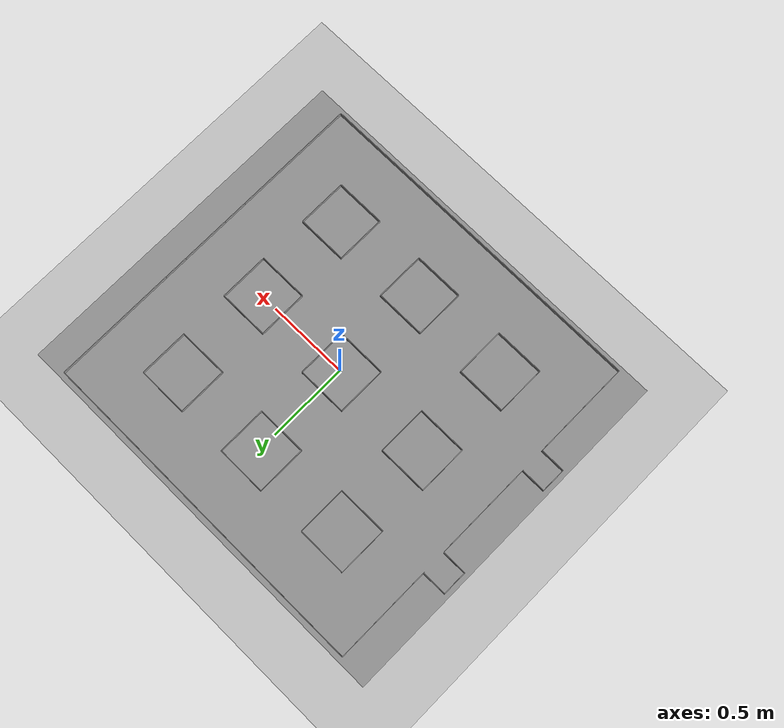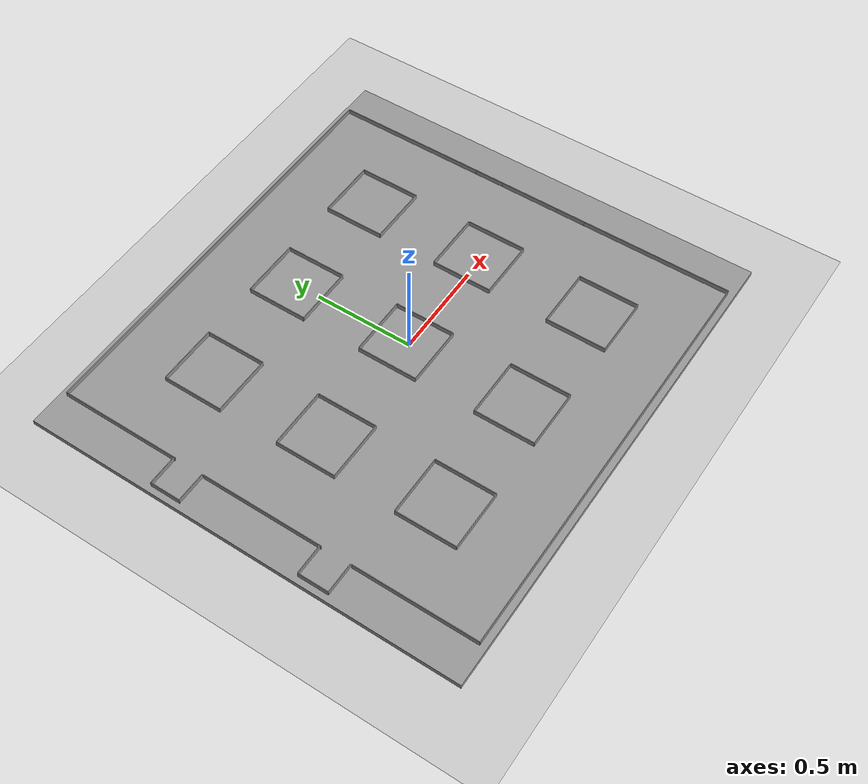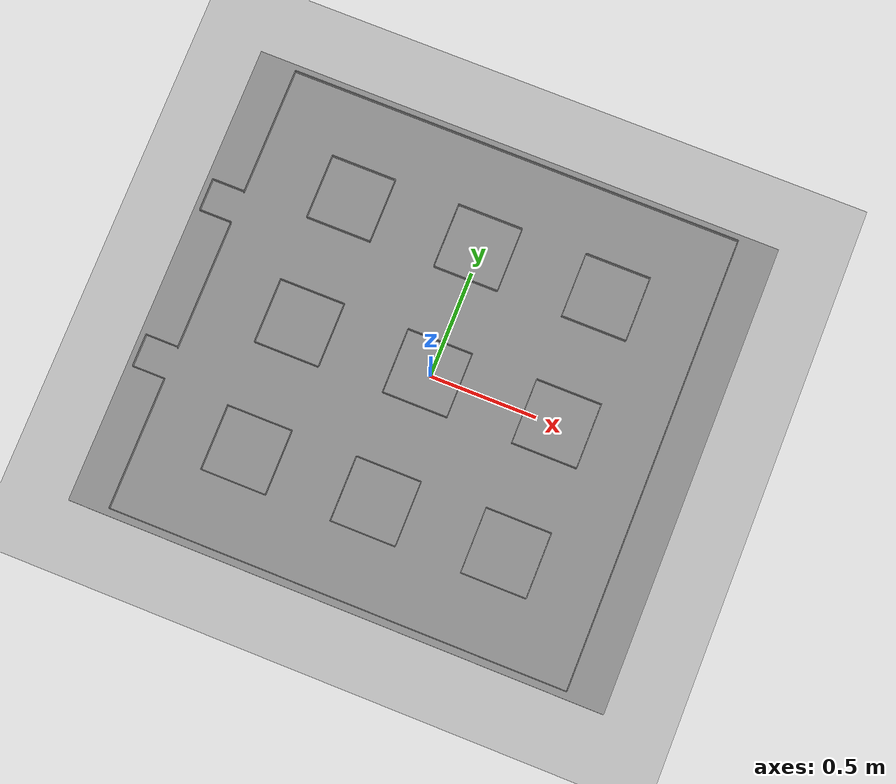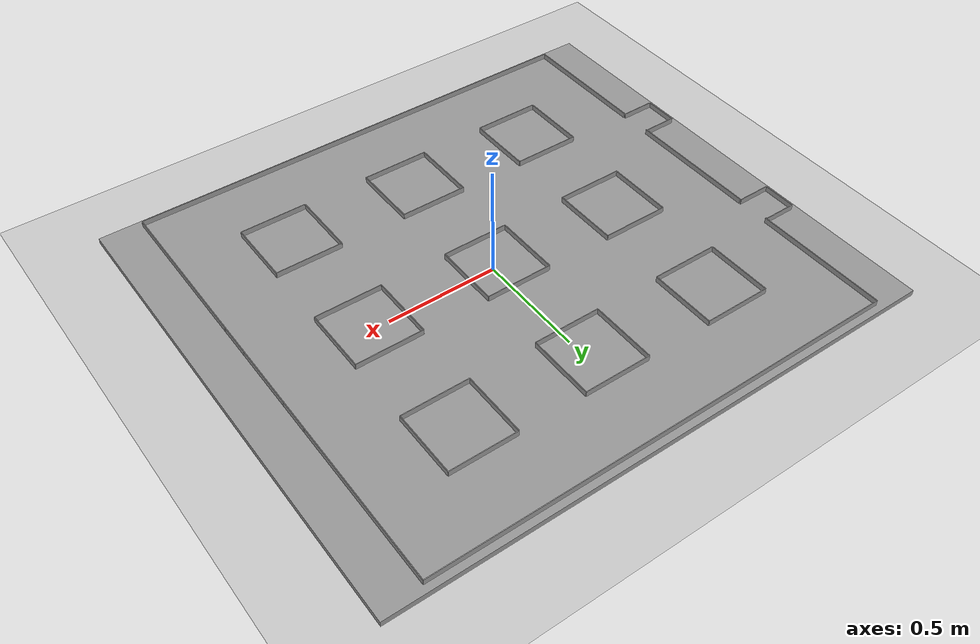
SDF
<sdf version="1.7">
 <world name="default">
  <light name="sun" type="directional">
   <pose>0 0 10 0 -0 0</pose>
   <diffuse>0.8 0.8 0.8 1</diffuse>
   <specular>0.2 0.2 0.2 1</specular>
   <attenuation>
    <range>1000</range>
    <constant>0.9</constant>
    <linear>0.01</linear>
    <quadratic>0.001</quadratic>
   </attenuation>
   <direction>-0.5 0.1 -0.9</direction>
   <spot><inner_angle>0</inner_angle><outer_angle>0</outer_angle><falloff>0</falloff></spot>
  </light>
  <model name="ground_plane">
   <static>1</static>
   <link name="link">
    <collision name="collision">
     <geometry><plane><normal>0 0 1</normal><size>100 100</size></plane></geometry>
     <surface>
      <contact><collide_bitmask>65535</collide_bitmask></contact>
      <friction><ode><mu>100</mu><mu2>50</mu2></ode></friction>
     </surface>
    </collision>
    <visual name="visual">
     <cast_shadows>0</cast_shadows>
     <geometry><plane><normal>0 0 1</normal><size>100 100</size></plane></geometry>
     <material>
      <script><uri>file://media/materials/scripts/gazebo.material</uri><name>Gazebo/Grey</name></script>
     </material>
    </visual>
   </link>
  </model>
  <gravity>0 0 -9.8</gravity>
  <magnetic_field>6e-06 2.3e-05 -4.2e-05</magnetic_field>
  <atmosphere type="adiabatic"/>
  <physics type="ode">
   <max_step_size>0.001</max_step_size>
   <real_time_factor>1</real_time_factor>
   <real_time_update_rate>1000</real_time_update_rate>
  </physics>
  <scene><ambient>0.4 0.4 0.4 1</ambient><background>0.7 0.7 0.7 1</background><shadows>1</shadows></scene>
  <spherical_coordinates>
   <surface_model>EARTH_WGS84</surface_model>
   <latitude_deg>0</latitude_deg>
   <longitude_deg>0</longitude_deg>
   <elevation>0</elevation>
   <heading_deg>0</heading_deg>
  </spherical_coordinates>
  <model name="696">
   <model name="ps2_nosignal">
    <link name="link_0">
     <inertial>
      <mass>1</mass>
      <inertia>
       <ixx>0.166667</ixx>
       <ixy>0</ixy>
       <ixz>0</ixz>
       <iyy>0.166667</iyy>
       <iyz>0</iyz>
       <izz>0.166667</izz>
      </inertia>
     </inertial>
     <pose>-7e-06 0.1524 0.000446 0 -0 0</pose>
     <visual name="visual">
      <geometry><box><size>0.3048 0.003175 0.0254</size></box></geometry>
      <material>
       <lighting>1</lighting>
       <script><uri>file://media/materials/scripts/gazebo.material</uri><name>Gazebo/Grey</name></script>
       <shader type="pixel"><normal_map>__default__</normal_map></shader>
       <ambient>0.3 0.3 0.3 1</ambient>
       <diffuse>0.7 0.7 0.7 1</diffuse>
       <specular>0.01 0.01 0.01 1</specular>
       <emissive>0 0 0 1</emissive>
      </material>
     </visual>
     <collision name="collision">
      <geometry><box><size>0.3048 0.003175 0.0254</size></box></geometry>
      <surface>
       <friction>
        <ode><mu>1</mu><mu2>1</mu2><fdir1>0 0 0</fdir1><slip1>0</slip1><slip2>0</slip2></ode>
        <torsional>
         <coefficient>1</coefficient>
         <patch_radius>0</patch_radius>
         <surface_radius>0</surface_radius>
         <use_patch_radius>1</use_patch_radius>
         <ode><slip>0</slip></ode>
        </torsional>
       </friction>
       <bounce><restitution_coefficient>0</restitution_coefficient><threshold>1e+06</threshold></bounce>
       <contact>
        <collide_without_contact>0</collide_without_contact>
        <collide_without_contact_bitmask>1</collide_without_contact_bitmask>
        <collide_bitmask>1</collide_bitmask>
        <ode>
         <soft_cfm>0</soft_cfm>
         <soft_erp>0.2</soft_erp>
         <kp>1e+13</kp>
         <kd>1</kd>
         <max_vel>0.01</max_vel>
         <min_depth>0</min_depth>
        </ode>
        <bullet>
         <split_impulse>1</split_impulse>
         <split_impulse_penetration_threshold>-0.01</split_impulse_penetration_threshold>
         <soft_cfm>0</soft_cfm>
         <soft_erp>0.2</soft_erp>
         <kp>1e+13</kp>
         <kd>1</kd>
        </bullet>
       </contact>
      </surface>
     </collision>
    </link>
    <link name="link_0_clone">
     <inertial>
      <mass>1</mass>
      <inertia>
       <ixx>0.166667</ixx>
       <ixy>0</ixy>
       <ixz>0</ixz>
       <iyy>0.166667</iyy>
       <iyz>0</iyz>
       <izz>0.166667</izz>
      </inertia>
     </inertial>
     <pose>-7e-06 -0.1524 0.000446 0 -0 0</pose>
     <visual name="visual">
      <geometry><box><size>0.3048 0.003175 0.0254</size></box></geometry>
      <material>
       <lighting>1</lighting>
       <script><uri>file://media/materials/scripts/gazebo.material</uri><name>Gazebo/Grey</name></script>
       <shader type="pixel"><normal_map>__default__</normal_map></shader>
       <ambient>0.3 0.3 0.3 1</ambient>
       <diffuse>0.7 0.7 0.7 1</diffuse>
       <specular>0.01 0.01 0.01 1</specular>
       <emissive>0 0 0 1</emissive>
      </material>
     </visual>
     <collision name="collision">
      <geometry><box><size>0.3048 0.003175 0.0254</size></box></geometry>
      <surface>
       <friction>
        <ode><mu>1</mu><mu2>1</mu2><fdir1>0 0 0</fdir1><slip1>0</slip1><slip2>0</slip2></ode>
        <torsional>
         <coefficient>1</coefficient>
         <patch_radius>0</patch_radius>
         <surface_radius>0</surface_radius>
         <use_patch_radius>1</use_patch_radius>
         <ode><slip>0</slip></ode>
        </torsional>
       </friction>
       <bounce><restitution_coefficient>0</restitution_coefficient><threshold>1e+06</threshold></bounce>
       <contact>
        <collide_without_contact>0</collide_without_contact>
        <collide_without_contact_bitmask>1</collide_without_contact_bitmask>
        <collide_bitmask>1</collide_bitmask>
        <ode>
         <soft_cfm>0</soft_cfm>
         <soft_erp>0.2</soft_erp>
         <kp>1e+13</kp>
         <kd>1</kd>
         <max_vel>0.01</max_vel>
         <min_depth>0</min_depth>
        </ode>
        <bullet>
         <split_impulse>1</split_impulse>
         <split_impulse_penetration_threshold>-0.01</split_impulse_penetration_threshold>
         <soft_cfm>0</soft_cfm>
         <soft_erp>0.2</soft_erp>
         <kp>1e+13</kp>
         <kd>1</kd>
        </bullet>
       </contact>
      </surface>
     </collision>
    </link>
    <link name="link_0_clone_0">
     <inertial>
      <mass>1</mass>
      <inertia>
       <ixx>0.166667</ixx>
       <ixy>0</ixy>
       <ixz>0</ixz>
       <iyy>0.166667</iyy>
       <iyz>0</iyz>
       <izz>0.166667</izz>
      </inertia>
     </inertial>
     <pose>-7e-06 0.4572 0.000446 0 -0 0</pose>
     <visual name="visual">
      <geometry><box><size>0.3048 0.003175 0.0254</size></box></geometry>
      <material>
       <lighting>1</lighting>
       <script><uri>file://media/materials/scripts/gazebo.material</uri><name>Gazebo/Grey</name></script>
       <shader type="pixel"><normal_map>__default__</normal_map></shader>
       <ambient>0.3 0.3 0.3 1</ambient>
       <diffuse>0.7 0.7 0.7 1</diffuse>
       <specular>0.01 0.01 0.01 1</specular>
       <emissive>0 0 0 1</emissive>
      </material>
     </visual>
     <collision name="collision">
      <geometry><box><size>0.3048 0.003175 0.0254</size></box></geometry>
      <surface>
       <friction>
        <ode><mu>1</mu><mu2>1</mu2><fdir1>0 0 0</fdir1><slip1>0</slip1><slip2>0</slip2></ode>
        <torsional>
         <coefficient>1</coefficient>
         <patch_radius>0</patch_radius>
         <surface_radius>0</surface_radius>
         <use_patch_radius>1</use_patch_radius>
         <ode><slip>0</slip></ode>
        </torsional>
       </friction>
       <bounce><restitution_coefficient>0</restitution_coefficient><threshold>1e+06</threshold></bounce>
       <contact>
        <collide_without_contact>0</collide_without_contact>
        <collide_without_contact_bitmask>1</collide_without_contact_bitmask>
        <collide_bitmask>1</collide_bitmask>
        <ode>
         <soft_cfm>0</soft_cfm>
         <soft_erp>0.2</soft_erp>
         <kp>1e+13</kp>
         <kd>1</kd>
         <max_vel>0.01</max_vel>
         <min_depth>0</min_depth>
        </ode>
        <bullet>
         <split_impulse>1</split_impulse>
         <split_impulse_penetration_threshold>-0.01</split_impulse_penetration_threshold>
         <soft_cfm>0</soft_cfm>
         <soft_erp>0.2</soft_erp>
         <kp>1e+13</kp>
         <kd>1</kd>
        </bullet>
       </contact>
      </surface>
     </collision>
    </link>
    <link name="link_0_clone_1">
     <inertial>
      <mass>1</mass>
      <inertia>
       <ixx>0.166667</ixx>
       <ixy>0</ixy>
       <ixz>0</ixz>
       <iyy>0.166667</iyy>
       <iyz>0</iyz>
       <izz>0.166667</izz>
      </inertia>
     </inertial>
     <pose>-7e-06 0.762 0.000446 0 -0 0</pose>
     <visual name="visual">
      <geometry><box><size>0.3048 0.003175 0.0254</size></box></geometry>
      <material>
       <lighting>1</lighting>
       <script><uri>file://media/materials/scripts/gazebo.material</uri><name>Gazebo/Grey</name></script>
       <shader type="pixel"><normal_map>__default__</normal_map></shader>
       <ambient>0.3 0.3 0.3 1</ambient>
       <diffuse>0.7 0.7 0.7 1</diffuse>
       <specular>0.01 0.01 0.01 1</specular>
       <emissive>0 0 0 1</emissive>
      </material>
     </visual>
     <collision name="collision">
      <geometry><box><size>0.3048 0.003175 0.0254</size></box></geometry>
      <surface>
       <friction>
        <ode><mu>1</mu><mu2>1</mu2><fdir1>0 0 0</fdir1><slip1>0</slip1><slip2>0</slip2></ode>
        <torsional>
         <coefficient>1</coefficient>
         <patch_radius>0</patch_radius>
         <surface_radius>0</surface_radius>
         <use_patch_radius>1</use_patch_radius>
         <ode><slip>0</slip></ode>
        </torsional>
       </friction>
       <bounce><restitution_coefficient>0</restitution_coefficient><threshold>1e+06</threshold></bounce>
       <contact>
        <collide_without_contact>0</collide_without_contact>
        <collide_without_contact_bitmask>1</collide_without_contact_bitmask>
        <collide_bitmask>1</collide_bitmask>
        <ode>
         <soft_cfm>0</soft_cfm>
         <soft_erp>0.2</soft_erp>
         <kp>1e+13</kp>
         <kd>1</kd>
         <max_vel>0.01</max_vel>
         <min_depth>0</min_depth>
        </ode>
        <bullet>
         <split_impulse>1</split_impulse>
         <split_impulse_penetration_threshold>-0.01</split_impulse_penetration_threshold>
         <soft_cfm>0</soft_cfm>
         <soft_erp>0.2</soft_erp>
         <kp>1e+13</kp>
         <kd>1</kd>
        </bullet>
       </contact>
      </surface>
     </collision>
    </link>
    <link name="link_0_clone_10">
     <inertial>
      <mass>1</mass>
      <inertia>
       <ixx>0.166667</ixx>
       <ixy>0</ixy>
       <ixz>0</ixz>
       <iyy>0.166667</iyy>
       <iyz>0</iyz>
       <izz>0.166667</izz>
      </inertia>
     </inertial>
     <pose>-0.609607 0.1524 0.000446 0 -0 0</pose>
     <visual name="visual">
      <geometry><box><size>0.3048 0.003175 0.0254</size></box></geometry>
      <material>
       <lighting>1</lighting>
       <script><uri>file://media/materials/scripts/gazebo.material</uri><name>Gazebo/Grey</name></script>
       <shader type="pixel"><normal_map>__default__</normal_map></shader>
       <ambient>0.3 0.3 0.3 1</ambient>
       <diffuse>0.7 0.7 0.7 1</diffuse>
       <specular>0.01 0.01 0.01 1</specular>
       <emissive>0 0 0 1</emissive>
      </material>
     </visual>
     <collision name="collision">
      <geometry><box><size>0.3048 0.003175 0.0254</size></box></geometry>
      <surface>
       <friction>
        <ode><mu>1</mu><mu2>1</mu2><fdir1>0 0 0</fdir1><slip1>0</slip1><slip2>0</slip2></ode>
        <torsional>
         <coefficient>1</coefficient>
         <patch_radius>0</patch_radius>
         <surface_radius>0</surface_radius>
         <use_patch_radius>1</use_patch_radius>
         <ode><slip>0</slip></ode>
        </torsional>
       </friction>
       <bounce><restitution_coefficient>0</restitution_coefficient><threshold>1e+06</threshold></bounce>
       <contact>
        <collide_without_contact>0</collide_without_contact>
        <collide_without_contact_bitmask>1</collide_without_contact_bitmask>
        <collide_bitmask>1</collide_bitmask>
        <ode>
         <soft_cfm>0</soft_cfm>
         <soft_erp>0.2</soft_erp>
         <kp>1e+13</kp>
         <kd>1</kd>
         <max_vel>0.01</max_vel>
         <min_depth>0</min_depth>
        </ode>
        <bullet>
         <split_impulse>1</split_impulse>
         <split_impulse_penetration_threshold>-0.01</split_impulse_penetration_threshold>
         <soft_cfm>0</soft_cfm>
         <soft_erp>0.2</soft_erp>
         <kp>1e+13</kp>
         <kd>1</kd>
        </bullet>
       </contact>
      </surface>
     </collision>
    </link>
    <link name="link_0_clone_11">
     <inertial>
      <mass>1</mass>
      <inertia>
       <ixx>0.166667</ixx>
       <ixy>0</ixy>
       <ixz>0</ixz>
       <iyy>0.166667</iyy>
       <iyz>0</iyz>
       <izz>0.166667</izz>
      </inertia>
     </inertial>
     <pose>-0.609607 -0.1524 0.000446 0 -0 0</pose>
     <visual name="visual">
      <geometry><box><size>0.3048 0.003175 0.0254</size></box></geometry>
      <material>
       <lighting>1</lighting>
       <script><uri>file://media/materials/scripts/gazebo.material</uri><name>Gazebo/Grey</name></script>
       <shader type="pixel"><normal_map>__default__</normal_map></shader>
       <ambient>0.3 0.3 0.3 1</ambient>
       <diffuse>0.7 0.7 0.7 1</diffuse>
       <specular>0.01 0.01 0.01 1</specular>
       <emissive>0 0 0 1</emissive>
      </material>
     </visual>
     <collision name="collision">
      <geometry><box><size>0.3048 0.003175 0.0254</size></box></geometry>
      <surface>
       <friction>
        <ode><mu>1</mu><mu2>1</mu2><fdir1>0 0 0</fdir1><slip1>0</slip1><slip2>0</slip2></ode>
        <torsional>
         <coefficient>1</coefficient>
         <patch_radius>0</patch_radius>
         <surface_radius>0</surface_radius>
         <use_patch_radius>1</use_patch_radius>
         <ode><slip>0</slip></ode>
        </torsional>
       </friction>
       <bounce><restitution_coefficient>0</restitution_coefficient><threshold>1e+06</threshold></bounce>
       <contact>
        <collide_without_contact>0</collide_without_contact>
        <collide_without_contact_bitmask>1</collide_without_contact_bitmask>
        <collide_bitmask>1</collide_bitmask>
        <ode>
         <soft_cfm>0</soft_cfm>
         <soft_erp>0.2</soft_erp>
         <kp>1e+13</kp>
         <kd>1</kd>
         <max_vel>0.01</max_vel>
         <min_depth>0</min_depth>
        </ode>
        <bullet>
         <split_impulse>1</split_impulse>
         <split_impulse_penetration_threshold>-0.01</split_impulse_penetration_threshold>
         <soft_cfm>0</soft_cfm>
         <soft_erp>0.2</soft_erp>
         <kp>1e+13</kp>
         <kd>1</kd>
        </bullet>
       </contact>
      </surface>
     </collision>
    </link>
    <link name="link_0_clone_12">
     <inertial>
      <mass>1</mass>
      <inertia>
       <ixx>0.166667</ixx>
       <ixy>0</ixy>
       <ixz>0</ixz>
       <iyy>0.166667</iyy>
       <iyz>0</iyz>
       <izz>0.166667</izz>
      </inertia>
     </inertial>
     <pose>-0.609607 0.4572 0.000446 0 -0 0</pose>
     <visual name="visual">
      <geometry><box><size>0.3048 0.003175 0.0254</size></box></geometry>
      <material>
       <lighting>1</lighting>
       <script><uri>file://media/materials/scripts/gazebo.material</uri><name>Gazebo/Grey</name></script>
       <shader type="pixel"><normal_map>__default__</normal_map></shader>
       <ambient>0.3 0.3 0.3 1</ambient>
       <diffuse>0.7 0.7 0.7 1</diffuse>
       <specular>0.01 0.01 0.01 1</specular>
       <emissive>0 0 0 1</emissive>
      </material>
     </visual>
     <collision name="collision">
      <geometry><box><size>0.3048 0.003175 0.0254</size></box></geometry>
      <surface>
       <friction>
        <ode><mu>1</mu><mu2>1</mu2><fdir1>0 0 0</fdir1><slip1>0</slip1><slip2>0</slip2></ode>
        <torsional>
         <coefficient>1</coefficient>
         <patch_radius>0</patch_radius>
         <surface_radius>0</surface_radius>
         <use_patch_radius>1</use_patch_radius>
         <ode><slip>0</slip></ode>
        </torsional>
       </friction>
       <bounce><restitution_coefficient>0</restitution_coefficient><threshold>1e+06</threshold></bounce>
       <contact>
        <collide_without_contact>0</collide_without_contact>
        <collide_without_contact_bitmask>1</collide_without_contact_bitmask>
        <collide_bitmask>1</collide_bitmask>
        <ode>
         <soft_cfm>0</soft_cfm>
         <soft_erp>0.2</soft_erp>
         <kp>1e+13</kp>
         <kd>1</kd>
         <max_vel>0.01</max_vel>
         <min_depth>0</min_depth>
        </ode>
        <bullet>
         <split_impulse>1</split_impulse>
         <split_impulse_penetration_threshold>-0.01</split_impulse_penetration_threshold>
         <soft_cfm>0</soft_cfm>
         <soft_erp>0.2</soft_erp>
         <kp>1e+13</kp>
         <kd>1</kd>
        </bullet>
       </contact>
      </surface>
     </collision>
    </link>
    <link name="link_0_clone_13">
     <inertial>
      <mass>1</mass>
      <inertia>
       <ixx>0.166667</ixx>
       <ixy>0</ixy>
       <ixz>0</ixz>
       <iyy>0.166667</iyy>
       <iyz>0</iyz>
       <izz>0.166667</izz>
      </inertia>
     </inertial>
     <pose>-0.609607 -0.4572 0.000446 0 -0 0</pose>
     <visual name="visual">
      <geometry><box><size>0.3048 0.003175 0.0254</size></box></geometry>
      <material>
       <lighting>1</lighting>
       <script><uri>file://media/materials/scripts/gazebo.material</uri><name>Gazebo/Grey</name></script>
       <shader type="pixel"><normal_map>__default__</normal_map></shader>
       <ambient>0.3 0.3 0.3 1</ambient>
       <diffuse>0.7 0.7 0.7 1</diffuse>
       <specular>0.01 0.01 0.01 1</specular>
       <emissive>0 0 0 1</emissive>
      </material>
     </visual>
     <collision name="collision">
      <geometry><box><size>0.3048 0.003175 0.0254</size></box></geometry>
      <surface>
       <friction>
        <ode><mu>1</mu><mu2>1</mu2><fdir1>0 0 0</fdir1><slip1>0</slip1><slip2>0</slip2></ode>
        <torsional>
         <coefficient>1</coefficient>
         <patch_radius>0</patch_radius>
         <surface_radius>0</surface_radius>
         <use_patch_radius>1</use_patch_radius>
         <ode><slip>0</slip></ode>
        </torsional>
       </friction>
       <bounce><restitution_coefficient>0</restitution_coefficient><threshold>1e+06</threshold></bounce>
       <contact>
        <collide_without_contact>0</collide_without_contact>
        <collide_without_contact_bitmask>1</collide_without_contact_bitmask>
        <collide_bitmask>1</collide_bitmask>
        <ode>
         <soft_cfm>0</soft_cfm>
         <soft_erp>0.2</soft_erp>
         <kp>1e+13</kp>
         <kd>1</kd>
         <max_vel>0.01</max_vel>
         <min_depth>0</min_depth>
        </ode>
        <bullet>
         <split_impulse>1</split_impulse>
         <split_impulse_penetration_threshold>-0.01</split_impulse_penetration_threshold>
         <soft_cfm>0</soft_cfm>
         <soft_erp>0.2</soft_erp>
         <kp>1e+13</kp>
         <kd>1</kd>
        </bullet>
       </contact>
      </surface>
     </collision>
    </link>
    <link name="link_0_clone_14">
     <inertial>
      <mass>1</mass>
      <inertia>
       <ixx>0.166667</ixx>
       <ixy>0</ixy>
       <ixz>0</ixz>
       <iyy>0.166667</iyy>
       <iyz>0</iyz>
       <izz>0.166667</izz>
      </inertia>
     </inertial>
     <pose>-0.609607 0.762 0.000446 0 -0 0</pose>
     <visual name="visual">
      <geometry><box><size>0.3048 0.003175 0.0254</size></box></geometry>
      <material>
       <lighting>1</lighting>
       <script><uri>file://media/materials/scripts/gazebo.material</uri><name>Gazebo/Grey</name></script>
       <shader type="pixel"><normal_map>__default__</normal_map></shader>
       <ambient>0.3 0.3 0.3 1</ambient>
       <diffuse>0.7 0.7 0.7 1</diffuse>
       <specular>0.01 0.01 0.01 1</specular>
       <emissive>0 0 0 1</emissive>
      </material>
     </visual>
     <collision name="collision">
      <geometry><box><size>0.3048 0.003175 0.0254</size></box></geometry>
      <surface>
       <friction>
        <ode><mu>1</mu><mu2>1</mu2><fdir1>0 0 0</fdir1><slip1>0</slip1><slip2>0</slip2></ode>
        <torsional>
         <coefficient>1</coefficient>
         <patch_radius>0</patch_radius>
         <surface_radius>0</surface_radius>
         <use_patch_radius>1</use_patch_radius>
         <ode><slip>0</slip></ode>
        </torsional>
       </friction>
       <bounce><restitution_coefficient>0</restitution_coefficient><threshold>1e+06</threshold></bounce>
       <contact>
        <collide_without_contact>0</collide_without_contact>
        <collide_without_contact_bitmask>1</collide_without_contact_bitmask>
        <collide_bitmask>1</collide_bitmask>
        <ode>
         <soft_cfm>0</soft_cfm>
         <soft_erp>0.2</soft_erp>
         <kp>1e+13</kp>
         <kd>1</kd>
         <max_vel>0.01</max_vel>
         <min_depth>0</min_depth>
        </ode>
        <bullet>
         <split_impulse>1</split_impulse>
         <split_impulse_penetration_threshold>-0.01</split_impulse_penetration_threshold>
         <soft_cfm>0</soft_cfm>
         <soft_erp>0.2</soft_erp>
         <kp>1e+13</kp>
         <kd>1</kd>
        </bullet>
       </contact>
      </surface>
     </collision>
    </link>
    <link name="link_0_clone_15">
     <inertial>
      <mass>1</mass>
      <inertia>
       <ixx>0.166667</ixx>
       <ixy>0</ixy>
       <ixz>0</ixz>
       <iyy>0.166667</iyy>
       <iyz>0</iyz>
       <izz>0.166667</izz>
      </inertia>
     </inertial>
     <pose>-0.609207 -0.762 0.000446 0 -0 0</pose>
     <visual name="visual">
      <geometry><box><size>0.3048 0.003175 0.0254</size></box></geometry>
      <material>
       <lighting>1</lighting>
       <script><uri>file://media/materials/scripts/gazebo.material</uri><name>Gazebo/Grey</name></script>
       <shader type="pixel"><normal_map>__default__</normal_map></shader>
       <ambient>0.3 0.3 0.3 1</ambient>
       <diffuse>0.7 0.7 0.7 1</diffuse>
       <specular>0.01 0.01 0.01 1</specular>
       <emissive>0 0 0 1</emissive>
      </material>
     </visual>
     <collision name="collision">
      <geometry><box><size>0.3048 0.003175 0.0254</size></box></geometry>
      <surface>
       <friction>
        <ode><mu>1</mu><mu2>1</mu2><fdir1>0 0 0</fdir1><slip1>0</slip1><slip2>0</slip2></ode>
        <torsional>
         <coefficient>1</coefficient>
         <patch_radius>0</patch_radius>
         <surface_radius>0</surface_radius>
         <use_patch_radius>1</use_patch_radius>
         <ode><slip>0</slip></ode>
        </torsional>
       </friction>
       <bounce><restitution_coefficient>0</restitution_coefficient><threshold>1e+06</threshold></bounce>
       <contact>
        <collide_without_contact>0</collide_without_contact>
        <collide_without_contact_bitmask>1</collide_without_contact_bitmask>
        <collide_bitmask>1</collide_bitmask>
        <ode>
         <soft_cfm>0</soft_cfm>
         <soft_erp>0.2</soft_erp>
         <kp>1e+13</kp>
         <kd>1</kd>
         <max_vel>0.01</max_vel>
         <min_depth>0</min_depth>
        </ode>
        <bullet>
         <split_impulse>1</split_impulse>
         <split_impulse_penetration_threshold>-0.01</split_impulse_penetration_threshold>
         <soft_cfm>0</soft_cfm>
         <soft_erp>0.2</soft_erp>
         <kp>1e+13</kp>
         <kd>1</kd>
        </bullet>
       </contact>
      </surface>
     </collision>
    </link>
    <link name="link_0_clone_2">
     <inertial>
      <mass>1</mass>
      <inertia>
       <ixx>0.166667</ixx>
       <ixy>0</ixy>
       <ixz>0</ixz>
       <iyy>0.166667</iyy>
       <iyz>0</iyz>
       <izz>0.166667</izz>
      </inertia>
     </inertial>
     <pose>-7e-06 -0.4572 0.000446 0 -0 0</pose>
     <visual name="visual">
      <geometry><box><size>0.3048 0.003175 0.0254</size></box></geometry>
      <material>
       <lighting>1</lighting>
       <script><uri>file://media/materials/scripts/gazebo.material</uri><name>Gazebo/Grey</name></script>
       <shader type="pixel"><normal_map>__default__</normal_map></shader>
       <ambient>0.3 0.3 0.3 1</ambient>
       <diffuse>0.7 0.7 0.7 1</diffuse>
       <specular>0.01 0.01 0.01 1</specular>
       <emissive>0 0 0 1</emissive>
      </material>
     </visual>
     <collision name="collision">
      <geometry><box><size>0.3048 0.003175 0.0254</size></box></geometry>
      <surface>
       <friction>
        <ode><mu>1</mu><mu2>1</mu2><fdir1>0 0 0</fdir1><slip1>0</slip1><slip2>0</slip2></ode>
        <torsional>
         <coefficient>1</coefficient>
         <patch_radius>0</patch_radius>
         <surface_radius>0</surface_radius>
         <use_patch_radius>1</use_patch_radius>
         <ode><slip>0</slip></ode>
        </torsional>
       </friction>
       <bounce><restitution_coefficient>0</restitution_coefficient><threshold>1e+06</threshold></bounce>
       <contact>
        <collide_without_contact>0</collide_without_contact>
        <collide_without_contact_bitmask>1</collide_without_contact_bitmask>
        <collide_bitmask>1</collide_bitmask>
        <ode>
         <soft_cfm>0</soft_cfm>
         <soft_erp>0.2</soft_erp>
         <kp>1e+13</kp>
         <kd>1</kd>
         <max_vel>0.01</max_vel>
         <min_depth>0</min_depth>
        </ode>
        <bullet>
         <split_impulse>1</split_impulse>
         <split_impulse_penetration_threshold>-0.01</split_impulse_penetration_threshold>
         <soft_cfm>0</soft_cfm>
         <soft_erp>0.2</soft_erp>
         <kp>1e+13</kp>
         <kd>1</kd>
        </bullet>
       </contact>
      </surface>
     </collision>
    </link>
    <link name="link_0_clone_3">
     <inertial>
      <mass>1</mass>
      <inertia>
       <ixx>0.166667</ixx>
       <ixy>0</ixy>
       <ixz>0</ixz>
       <iyy>0.166667</iyy>
       <iyz>0</iyz>
       <izz>0.166667</izz>
      </inertia>
     </inertial>
     <pose>-7e-06 -0.762 0.000446 0 -0 0</pose>
     <visual name="visual">
      <geometry><box><size>0.3048 0.003175 0.0254</size></box></geometry>
      <material>
       <lighting>1</lighting>
       <script><uri>file://media/materials/scripts/gazebo.material</uri><name>Gazebo/Grey</name></script>
       <shader type="pixel"><normal_map>__default__</normal_map></shader>
       <ambient>0.3 0.3 0.3 1</ambient>
       <diffuse>0.7 0.7 0.7 1</diffuse>
       <specular>0.01 0.01 0.01 1</specular>
       <emissive>0 0 0 1</emissive>
      </material>
     </visual>
     <collision name="collision">
      <geometry><box><size>0.3048 0.003175 0.0254</size></box></geometry>
      <surface>
       <friction>
        <ode><mu>1</mu><mu2>1</mu2><fdir1>0 0 0</fdir1><slip1>0</slip1><slip2>0</slip2></ode>
        <torsional>
         <coefficient>1</coefficient>
         <patch_radius>0</patch_radius>
         <surface_radius>0</surface_radius>
         <use_patch_radius>1</use_patch_radius>
         <ode><slip>0</slip></ode>
        </torsional>
       </friction>
       <bounce><restitution_coefficient>0</restitution_coefficient><threshold>1e+06</threshold></bounce>
       <contact>
        <collide_without_contact>0</collide_without_contact>
        <collide_without_contact_bitmask>1</collide_without_contact_bitmask>
        <collide_bitmask>1</collide_bitmask>
        <ode>
         <soft_cfm>0</soft_cfm>
         <soft_erp>0.2</soft_erp>
         <kp>1e+13</kp>
         <kd>1</kd>
         <max_vel>0.01</max_vel>
         <min_depth>0</min_depth>
        </ode>
        <bullet>
         <split_impulse>1</split_impulse>
         <split_impulse_penetration_threshold>-0.01</split_impulse_penetration_threshold>
         <soft_cfm>0</soft_cfm>
         <soft_erp>0.2</soft_erp>
         <kp>1e+13</kp>
         <kd>1</kd>
        </bullet>
       </contact>
      </surface>
     </collision>
    </link>
    <link name="link_0_clone_4">
     <inertial>
      <mass>1</mass>
      <inertia>
       <ixx>0.166667</ixx>
       <ixy>0</ixy>
       <ixz>0</ixz>
       <iyy>0.166667</iyy>
       <iyz>0</iyz>
       <izz>0.166667</izz>
      </inertia>
     </inertial>
     <pose>0.609593 0.762 0.000446 0 -0 0</pose>
     <visual name="visual">
      <geometry><box><size>0.3048 0.003175 0.0254</size></box></geometry>
      <material>
       <lighting>1</lighting>
       <script><uri>file://media/materials/scripts/gazebo.material</uri><name>Gazebo/Grey</name></script>
       <shader type="pixel"><normal_map>__default__</normal_map></shader>
       <ambient>0.3 0.3 0.3 1</ambient>
       <diffuse>0.7 0.7 0.7 1</diffuse>
       <specular>0.01 0.01 0.01 1</specular>
       <emissive>0 0 0 1</emissive>
      </material>
     </visual>
     <collision name="collision">
      <geometry><box><size>0.3048 0.003175 0.0254</size></box></geometry>
      <surface>
       <friction>
        <ode><mu>1</mu><mu2>1</mu2><fdir1>0 0 0</fdir1><slip1>0</slip1><slip2>0</slip2></ode>
        <torsional>
         <coefficient>1</coefficient>
         <patch_radius>0</patch_radius>
         <surface_radius>0</surface_radius>
         <use_patch_radius>1</use_patch_radius>
         <ode><slip>0</slip></ode>
        </torsional>
       </friction>
       <bounce><restitution_coefficient>0</restitution_coefficient><threshold>1e+06</threshold></bounce>
       <contact>
        <collide_without_contact>0</collide_without_contact>
        <collide_without_contact_bitmask>1</collide_without_contact_bitmask>
        <collide_bitmask>1</collide_bitmask>
        <ode>
         <soft_cfm>0</soft_cfm>
         <soft_erp>0.2</soft_erp>
         <kp>1e+13</kp>
         <kd>1</kd>
         <max_vel>0.01</max_vel>
         <min_depth>0</min_depth>
        </ode>
        <bullet>
         <split_impulse>1</split_impulse>
         <split_impulse_penetration_threshold>-0.01</split_impulse_penetration_threshold>
         <soft_cfm>0</soft_cfm>
         <soft_erp>0.2</soft_erp>
         <kp>1e+13</kp>
         <kd>1</kd>
        </bullet>
       </contact>
      </surface>
     </collision>
    </link>
    <link name="link_0_clone_5">
     <inertial>
      <mass>1</mass>
      <inertia>
       <ixx>0.166667</ixx>
       <ixy>0</ixy>
       <ixz>0</ixz>
       <iyy>0.166667</iyy>
       <iyz>0</iyz>
       <izz>0.166667</izz>
      </inertia>
     </inertial>
     <pose>0.609593 0.4572 0.000446 0 -0 0</pose>
     <visual name="visual">
      <geometry><box><size>0.3048 0.003175 0.0254</size></box></geometry>
      <material>
       <lighting>1</lighting>
       <script><uri>file://media/materials/scripts/gazebo.material</uri><name>Gazebo/Grey</name></script>
       <shader type="pixel"><normal_map>__default__</normal_map></shader>
       <ambient>0.3 0.3 0.3 1</ambient>
       <diffuse>0.7 0.7 0.7 1</diffuse>
       <specular>0.01 0.01 0.01 1</specular>
       <emissive>0 0 0 1</emissive>
      </material>
     </visual>
     <collision name="collision">
      <geometry><box><size>0.3048 0.003175 0.0254</size></box></geometry>
      <surface>
       <friction>
        <ode><mu>1</mu><mu2>1</mu2><fdir1>0 0 0</fdir1><slip1>0</slip1><slip2>0</slip2></ode>
        <torsional>
         <coefficient>1</coefficient>
         <patch_radius>0</patch_radius>
         <surface_radius>0</surface_radius>
         <use_patch_radius>1</use_patch_radius>
         <ode><slip>0</slip></ode>
        </torsional>
       </friction>
       <bounce><restitution_coefficient>0</restitution_coefficient><threshold>1e+06</threshold></bounce>
       <contact>
        <collide_without_contact>0</collide_without_contact>
        <collide_without_contact_bitmask>1</collide_without_contact_bitmask>
        <collide_bitmask>1</collide_bitmask>
        <ode>
         <soft_cfm>0</soft_cfm>
         <soft_erp>0.2</soft_erp>
         <kp>1e+13</kp>
         <kd>1</kd>
         <max_vel>0.01</max_vel>
         <min_depth>0</min_depth>
        </ode>
        <bullet>
         <split_impulse>1</split_impulse>
         <split_impulse_penetration_threshold>-0.01</split_impulse_penetration_threshold>
         <soft_cfm>0</soft_cfm>
         <soft_erp>0.2</soft_erp>
         <kp>1e+13</kp>
         <kd>1</kd>
        </bullet>
       </contact>
      </surface>
     </collision>
    </link>
    <link name="link_0_clone_6">
     <inertial>
      <mass>1</mass>
      <inertia>
       <ixx>0.166667</ixx>
       <ixy>0</ixy>
       <ixz>0</ixz>
       <iyy>0.166667</iyy>
       <iyz>0</iyz>
       <izz>0.166667</izz>
      </inertia>
     </inertial>
     <pose>0.609593 0.1524 0.000446 0 -0 0</pose>
     <visual name="visual">
      <geometry><box><size>0.3048 0.003175 0.0254</size></box></geometry>
      <material>
       <lighting>1</lighting>
       <script><uri>file://media/materials/scripts/gazebo.material</uri><name>Gazebo/Grey</name></script>
       <shader type="pixel"><normal_map>__default__</normal_map></shader>
       <ambient>0.3 0.3 0.3 1</ambient>
       <diffuse>0.7 0.7 0.7 1</diffuse>
       <specular>0.01 0.01 0.01 1</specular>
       <emissive>0 0 0 1</emissive>
      </material>
     </visual>
     <collision name="collision">
      <geometry><box><size>0.3048 0.003175 0.0254</size></box></geometry>
      <surface>
       <friction>
        <ode><mu>1</mu><mu2>1</mu2><fdir1>0 0 0</fdir1><slip1>0</slip1><slip2>0</slip2></ode>
        <torsional>
         <coefficient>1</coefficient>
         <patch_radius>0</patch_radius>
         <surface_radius>0</surface_radius>
         <use_patch_radius>1</use_patch_radius>
         <ode><slip>0</slip></ode>
        </torsional>
       </friction>
       <bounce><restitution_coefficient>0</restitution_coefficient><threshold>1e+06</threshold></bounce>
       <contact>
        <collide_without_contact>0</collide_without_contact>
        <collide_without_contact_bitmask>1</collide_without_contact_bitmask>
        <collide_bitmask>1</collide_bitmask>
        <ode>
         <soft_cfm>0</soft_cfm>
         <soft_erp>0.2</soft_erp>
         <kp>1e+13</kp>
         <kd>1</kd>
         <max_vel>0.01</max_vel>
         <min_depth>0</min_depth>
        </ode>
        <bullet>
         <split_impulse>1</split_impulse>
         <split_impulse_penetration_threshold>-0.01</split_impulse_penetration_threshold>
         <soft_cfm>0</soft_cfm>
         <soft_erp>0.2</soft_erp>
         <kp>1e+13</kp>
         <kd>1</kd>
        </bullet>
       </contact>
      </surface>
     </collision>
    </link>
    <link name="link_0_clone_7">
     <inertial>
      <mass>1</mass>
      <inertia>
       <ixx>0.166667</ixx>
       <ixy>0</ixy>
       <ixz>0</ixz>
       <iyy>0.166667</iyy>
       <iyz>0</iyz>
       <izz>0.166667</izz>
      </inertia>
     </inertial>
     <pose>0.609593 -0.1524 0.000446 0 -0 0</pose>
     <visual name="visual">
      <geometry><box><size>0.3048 0.003175 0.0254</size></box></geometry>
      <material>
       <lighting>1</lighting>
       <script><uri>file://media/materials/scripts/gazebo.material</uri><name>Gazebo/Grey</name></script>
       <shader type="pixel"><normal_map>__default__</normal_map></shader>
       <ambient>0.3 0.3 0.3 1</ambient>
       <diffuse>0.7 0.7 0.7 1</diffuse>
       <specular>0.01 0.01 0.01 1</specular>
       <emissive>0 0 0 1</emissive>
      </material>
     </visual>
     <collision name="collision">
      <geometry><box><size>0.3048 0.003175 0.0254</size></box></geometry>
      <surface>
       <friction>
        <ode><mu>1</mu><mu2>1</mu2><fdir1>0 0 0</fdir1><slip1>0</slip1><slip2>0</slip2></ode>
        <torsional>
         <coefficient>1</coefficient>
         <patch_radius>0</patch_radius>
         <surface_radius>0</surface_radius>
         <use_patch_radius>1</use_patch_radius>
         <ode><slip>0</slip></ode>
        </torsional>
       </friction>
       <bounce><restitution_coefficient>0</restitution_coefficient><threshold>1e+06</threshold></bounce>
       <contact>
        <collide_without_contact>0</collide_without_contact>
        <collide_without_contact_bitmask>1</collide_without_contact_bitmask>
        <collide_bitmask>1</collide_bitmask>
        <ode>
         <soft_cfm>0</soft_cfm>
         <soft_erp>0.2</soft_erp>
         <kp>1e+13</kp>
         <kd>1</kd>
         <max_vel>0.01</max_vel>
         <min_depth>0</min_depth>
        </ode>
        <bullet>
         <split_impulse>1</split_impulse>
         <split_impulse_penetration_threshold>-0.01</split_impulse_penetration_threshold>
         <soft_cfm>0</soft_cfm>
         <soft_erp>0.2</soft_erp>
         <kp>1e+13</kp>
         <kd>1</kd>
        </bullet>
       </contact>
      </surface>
     </collision>
    </link>
    <link name="link_0_clone_8">
     <inertial>
      <mass>1</mass>
      <inertia>
       <ixx>0.166667</ixx>
       <ixy>0</ixy>
       <ixz>0</ixz>
       <iyy>0.166667</iyy>
       <iyz>0</iyz>
       <izz>0.166667</izz>
      </inertia>
     </inertial>
     <pose>0.609593 -0.4572 0.000446 0 -0 0</pose>
     <visual name="visual">
      <geometry><box><size>0.3048 0.003175 0.0254</size></box></geometry>
      <material>
       <lighting>1</lighting>
       <script><uri>file://media/materials/scripts/gazebo.material</uri><name>Gazebo/Grey</name></script>
       <shader type="pixel"><normal_map>__default__</normal_map></shader>
       <ambient>0.3 0.3 0.3 1</ambient>
       <diffuse>0.7 0.7 0.7 1</diffuse>
       <specular>0.01 0.01 0.01 1</specular>
       <emissive>0 0 0 1</emissive>
      </material>
     </visual>
     <collision name="collision">
      <geometry><box><size>0.3048 0.003175 0.0254</size></box></geometry>
      <surface>
       <friction>
        <ode><mu>1</mu><mu2>1</mu2><fdir1>0 0 0</fdir1><slip1>0</slip1><slip2>0</slip2></ode>
        <torsional>
         <coefficient>1</coefficient>
         <patch_radius>0</patch_radius>
         <surface_radius>0</surface_radius>
         <use_patch_radius>1</use_patch_radius>
         <ode><slip>0</slip></ode>
        </torsional>
       </friction>
       <bounce><restitution_coefficient>0</restitution_coefficient><threshold>1e+06</threshold></bounce>
       <contact>
        <collide_without_contact>0</collide_without_contact>
        <collide_without_contact_bitmask>1</collide_without_contact_bitmask>
        <collide_bitmask>1</collide_bitmask>
        <ode>
         <soft_cfm>0</soft_cfm>
         <soft_erp>0.2</soft_erp>
         <kp>1e+13</kp>
         <kd>1</kd>
         <max_vel>0.01</max_vel>
         <min_depth>0</min_depth>
        </ode>
        <bullet>
         <split_impulse>1</split_impulse>
         <split_impulse_penetration_threshold>-0.01</split_impulse_penetration_threshold>
         <soft_cfm>0</soft_cfm>
         <soft_erp>0.2</soft_erp>
         <kp>1e+13</kp>
         <kd>1</kd>
        </bullet>
       </contact>
      </surface>
     </collision>
    </link>
    <link name="link_0_clone_9">
     <inertial>
      <mass>1</mass>
      <inertia>
       <ixx>0.166667</ixx>
       <ixy>0</ixy>
       <ixz>0</ixz>
       <iyy>0.166667</iyy>
       <iyz>0</iyz>
       <izz>0.166667</izz>
      </inertia>
     </inertial>
     <pose>0.609593 -0.762 0.000446 0 -0 0</pose>
     <visual name="visual">
      <geometry><box><size>0.3048 0.003175 0.0254</size></box></geometry>
      <material>
       <lighting>1</lighting>
       <script><uri>file://media/materials/scripts/gazebo.material</uri><name>Gazebo/Grey</name></script>
       <shader type="pixel"><normal_map>__default__</normal_map></shader>
       <ambient>0.3 0.3 0.3 1</ambient>
       <diffuse>0.7 0.7 0.7 1</diffuse>
       <specular>0.01 0.01 0.01 1</specular>
       <emissive>0 0 0 1</emissive>
      </material>
     </visual>
     <collision name="collision">
      <geometry><box><size>0.3048 0.003175 0.0254</size></box></geometry>
      <surface>
       <friction>
        <ode><mu>1</mu><mu2>1</mu2><fdir1>0 0 0</fdir1><slip1>0</slip1><slip2>0</slip2></ode>
        <torsional>
         <coefficient>1</coefficient>
         <patch_radius>0</patch_radius>
         <surface_radius>0</surface_radius>
         <use_patch_radius>1</use_patch_radius>
         <ode><slip>0</slip></ode>
        </torsional>
       </friction>
       <bounce><restitution_coefficient>0</restitution_coefficient><threshold>1e+06</threshold></bounce>
       <contact>
        <collide_without_contact>0</collide_without_contact>
        <collide_without_contact_bitmask>1</collide_without_contact_bitmask>
        <collide_bitmask>1</collide_bitmask>
        <ode>
         <soft_cfm>0</soft_cfm>
         <soft_erp>0.2</soft_erp>
         <kp>1e+13</kp>
         <kd>1</kd>
         <max_vel>0.01</max_vel>
         <min_depth>0</min_depth>
        </ode>
        <bullet>
         <split_impulse>1</split_impulse>
         <split_impulse_penetration_threshold>-0.01</split_impulse_penetration_threshold>
         <soft_cfm>0</soft_cfm>
         <soft_erp>0.2</soft_erp>
         <kp>1e+13</kp>
         <kd>1</kd>
        </bullet>
       </contact>
      </surface>
     </collision>
    </link>
    <link name="link_1">
     <inertial>
      <mass>1</mass>
      <inertia>
       <ixx>0.166667</ixx>
       <ixy>0</ixy>
       <ixz>0</ixz>
       <iyy>0.166667</iyy>
       <iyz>0</iyz>
       <izz>0.166667</izz>
      </inertia>
     </inertial>
     <pose>0.152393 0 0.000446 0 -0 0</pose>
     <visual name="visual">
      <geometry><box><size>0.003175 0.3048 0.0254</size></box></geometry>
      <material>
       <lighting>1</lighting>
       <script><uri>file://media/materials/scripts/gazebo.material</uri><name>Gazebo/Grey</name></script>
       <shader type="pixel"><normal_map>__default__</normal_map></shader>
       <ambient>0.3 0.3 0.3 1</ambient>
       <diffuse>0.7 0.7 0.7 1</diffuse>
       <specular>0.01 0.01 0.01 1</specular>
       <emissive>0 0 0 1</emissive>
      </material>
     </visual>
     <collision name="collision">
      <geometry><box><size>0.003175 0.3048 0.0254</size></box></geometry>
      <surface>
       <friction>
        <ode><mu>1</mu><mu2>1</mu2><fdir1>0 0 0</fdir1><slip1>0</slip1><slip2>0</slip2></ode>
        <torsional>
         <coefficient>1</coefficient>
         <patch_radius>0</patch_radius>
         <surface_radius>0</surface_radius>
         <use_patch_radius>1</use_patch_radius>
         <ode><slip>0</slip></ode>
        </torsional>
       </friction>
       <bounce><restitution_coefficient>0</restitution_coefficient><threshold>1e+06</threshold></bounce>
       <contact>
        <collide_without_contact>0</collide_without_contact>
        <collide_without_contact_bitmask>1</collide_without_contact_bitmask>
        <collide_bitmask>1</collide_bitmask>
        <ode>
         <soft_cfm>0</soft_cfm>
         <soft_erp>0.2</soft_erp>
         <kp>1e+13</kp>
         <kd>1</kd>
         <max_vel>0.01</max_vel>
         <min_depth>0</min_depth>
        </ode>
        <bullet>
         <split_impulse>1</split_impulse>
         <split_impulse_penetration_threshold>-0.01</split_impulse_penetration_threshold>
         <soft_cfm>0</soft_cfm>
         <soft_erp>0.2</soft_erp>
         <kp>1e+13</kp>
         <kd>1</kd>
        </bullet>
       </contact>
      </surface>
     </collision>
    </link>
    <link name="link_1_clone">
     <inertial>
      <mass>1</mass>
      <inertia>
       <ixx>0.166667</ixx>
       <ixy>0</ixy>
       <ixz>0</ixz>
       <iyy>0.166667</iyy>
       <iyz>0</iyz>
       <izz>0.166667</izz>
      </inertia>
     </inertial>
     <pose>-0.152407 0 0.000446 0 -0 0</pose>
     <visual name="visual">
      <geometry><box><size>0.003175 0.3048 0.0254</size></box></geometry>
      <material>
       <lighting>1</lighting>
       <script><uri>file://media/materials/scripts/gazebo.material</uri><name>Gazebo/Grey</name></script>
       <shader type="pixel"><normal_map>__default__</normal_map></shader>
       <ambient>0.3 0.3 0.3 1</ambient>
       <diffuse>0.7 0.7 0.7 1</diffuse>
       <specular>0.01 0.01 0.01 1</specular>
       <emissive>0 0 0 1</emissive>
      </material>
     </visual>
     <collision name="collision">
      <geometry><box><size>0.003175 0.3048 0.0254</size></box></geometry>
      <surface>
       <friction>
        <ode><mu>1</mu><mu2>1</mu2><fdir1>0 0 0</fdir1><slip1>0</slip1><slip2>0</slip2></ode>
        <torsional>
         <coefficient>1</coefficient>
         <patch_radius>0</patch_radius>
         <surface_radius>0</surface_radius>
         <use_patch_radius>1</use_patch_radius>
         <ode><slip>0</slip></ode>
        </torsional>
       </friction>
       <bounce><restitution_coefficient>0</restitution_coefficient><threshold>1e+06</threshold></bounce>
       <contact>
        <collide_without_contact>0</collide_without_contact>
        <collide_without_contact_bitmask>1</collide_without_contact_bitmask>
        <collide_bitmask>1</collide_bitmask>
        <ode>
         <soft_cfm>0</soft_cfm>
         <soft_erp>0.2</soft_erp>
         <kp>1e+13</kp>
         <kd>1</kd>
         <max_vel>0.01</max_vel>
         <min_depth>0</min_depth>
        </ode>
        <bullet>
         <split_impulse>1</split_impulse>
         <split_impulse_penetration_threshold>-0.01</split_impulse_penetration_threshold>
         <soft_cfm>0</soft_cfm>
         <soft_erp>0.2</soft_erp>
         <kp>1e+13</kp>
         <kd>1</kd>
        </bullet>
       </contact>
      </surface>
     </collision>
    </link>
    <link name="link_1_clone_0">
     <inertial>
      <mass>1</mass>
      <inertia>
       <ixx>0.166667</ixx>
       <ixy>0</ixy>
       <ixz>0</ixz>
       <iyy>0.166667</iyy>
       <iyz>0</iyz>
       <izz>0.166667</izz>
      </inertia>
     </inertial>
     <pose>0.457193 0 0.000446 0 -0 0</pose>
     <visual name="visual">
      <geometry><box><size>0.003175 0.3048 0.0254</size></box></geometry>
      <material>
       <lighting>1</lighting>
       <script><uri>file://media/materials/scripts/gazebo.material</uri><name>Gazebo/Grey</name></script>
       <shader type="pixel"><normal_map>__default__</normal_map></shader>
       <ambient>0.3 0.3 0.3 1</ambient>
       <diffuse>0.7 0.7 0.7 1</diffuse>
       <specular>0.01 0.01 0.01 1</specular>
       <emissive>0 0 0 1</emissive>
      </material>
     </visual>
     <collision name="collision">
      <geometry><box><size>0.003175 0.3048 0.0254</size></box></geometry>
      <surface>
       <friction>
        <ode><mu>1</mu><mu2>1</mu2><fdir1>0 0 0</fdir1><slip1>0</slip1><slip2>0</slip2></ode>
        <torsional>
         <coefficient>1</coefficient>
         <patch_radius>0</patch_radius>
         <surface_radius>0</surface_radius>
         <use_patch_radius>1</use_patch_radius>
         <ode><slip>0</slip></ode>
        </torsional>
       </friction>
       <bounce><restitution_coefficient>0</restitution_coefficient><threshold>1e+06</threshold></bounce>
       <contact>
        <collide_without_contact>0</collide_without_contact>
        <collide_without_contact_bitmask>1</collide_without_contact_bitmask>
        <collide_bitmask>1</collide_bitmask>
        <ode>
         <soft_cfm>0</soft_cfm>
         <soft_erp>0.2</soft_erp>
         <kp>1e+13</kp>
         <kd>1</kd>
         <max_vel>0.01</max_vel>
         <min_depth>0</min_depth>
        </ode>
        <bullet>
         <split_impulse>1</split_impulse>
         <split_impulse_penetration_threshold>-0.01</split_impulse_penetration_threshold>
         <soft_cfm>0</soft_cfm>
         <soft_erp>0.2</soft_erp>
         <kp>1e+13</kp>
         <kd>1</kd>
        </bullet>
       </contact>
      </surface>
     </collision>
    </link>
    <link name="link_1_clone_1">
     <inertial>
      <mass>1</mass>
      <inertia>
       <ixx>0.166667</ixx>
       <ixy>0</ixy>
       <ixz>0</ixz>
       <iyy>0.166667</iyy>
       <iyz>0</iyz>
       <izz>0.166667</izz>
      </inertia>
     </inertial>
     <pose>-0.457207 0 0.000446 0 -0 0</pose>
     <visual name="visual">
      <geometry><box><size>0.003175 0.3048 0.0254</size></box></geometry>
      <material>
       <lighting>1</lighting>
       <script><uri>file://media/materials/scripts/gazebo.material</uri><name>Gazebo/Grey</name></script>
       <shader type="pixel"><normal_map>__default__</normal_map></shader>
       <ambient>0.3 0.3 0.3 1</ambient>
       <diffuse>0.7 0.7 0.7 1</diffuse>
       <specular>0.01 0.01 0.01 1</specular>
       <emissive>0 0 0 1</emissive>
      </material>
     </visual>
     <collision name="collision">
      <geometry><box><size>0.003175 0.3048 0.0254</size></box></geometry>
      <surface>
       <friction>
        <ode><mu>1</mu><mu2>1</mu2><fdir1>0 0 0</fdir1><slip1>0</slip1><slip2>0</slip2></ode>
        <torsional>
         <coefficient>1</coefficient>
         <patch_radius>0</patch_radius>
         <surface_radius>0</surface_radius>
         <use_patch_radius>1</use_patch_radius>
         <ode><slip>0</slip></ode>
        </torsional>
       </friction>
       <bounce><restitution_coefficient>0</restitution_coefficient><threshold>1e+06</threshold></bounce>
       <contact>
        <collide_without_contact>0</collide_without_contact>
        <collide_without_contact_bitmask>1</collide_without_contact_bitmask>
        <collide_bitmask>1</collide_bitmask>
        <ode>
         <soft_cfm>0</soft_cfm>
         <soft_erp>0.2</soft_erp>
         <kp>1e+13</kp>
         <kd>1</kd>
         <max_vel>0.01</max_vel>
         <min_depth>0</min_depth>
        </ode>
        <bullet>
         <split_impulse>1</split_impulse>
         <split_impulse_penetration_threshold>-0.01</split_impulse_penetration_threshold>
         <soft_cfm>0</soft_cfm>
         <soft_erp>0.2</soft_erp>
         <kp>1e+13</kp>
         <kd>1</kd>
        </bullet>
       </contact>
      </surface>
     </collision>
    </link>
    <link name="link_1_clone_10">
     <inertial>
      <mass>1</mass>
      <inertia>
       <ixx>0.166667</ixx>
       <ixy>0</ixy>
       <ixz>0</ixz>
       <iyy>0.166667</iyy>
       <iyz>0</iyz>
       <izz>0.166667</izz>
      </inertia>
     </inertial>
     <pose>0.152393 -0.6096 0.000446 0 -0 0</pose>
     <visual name="visual">
      <geometry><box><size>0.003175 0.3048 0.0254</size></box></geometry>
      <material>
       <lighting>1</lighting>
       <script><uri>file://media/materials/scripts/gazebo.material</uri><name>Gazebo/Grey</name></script>
       <shader type="pixel"><normal_map>__default__</normal_map></shader>
       <ambient>0.3 0.3 0.3 1</ambient>
       <diffuse>0.7 0.7 0.7 1</diffuse>
       <specular>0.01 0.01 0.01 1</specular>
       <emissive>0 0 0 1</emissive>
      </material>
     </visual>
     <collision name="collision">
      <geometry><box><size>0.003175 0.3048 0.0254</size></box></geometry>
      <surface>
       <friction>
        <ode><mu>1</mu><mu2>1</mu2><fdir1>0 0 0</fdir1><slip1>0</slip1><slip2>0</slip2></ode>
        <torsional>
         <coefficient>1</coefficient>
         <patch_radius>0</patch_radius>
         <surface_radius>0</surface_radius>
         <use_patch_radius>1</use_patch_radius>
         <ode><slip>0</slip></ode>
        </torsional>
       </friction>
       <bounce><restitution_coefficient>0</restitution_coefficient><threshold>1e+06</threshold></bounce>
       <contact>
        <collide_without_contact>0</collide_without_contact>
        <collide_without_contact_bitmask>1</collide_without_contact_bitmask>
        <collide_bitmask>1</collide_bitmask>
        <ode>
         <soft_cfm>0</soft_cfm>
         <soft_erp>0.2</soft_erp>
         <kp>1e+13</kp>
         <kd>1</kd>
         <max_vel>0.01</max_vel>
         <min_depth>0</min_depth>
        </ode>
        <bullet>
         <split_impulse>1</split_impulse>
         <split_impulse_penetration_threshold>-0.01</split_impulse_penetration_threshold>
         <soft_cfm>0</soft_cfm>
         <soft_erp>0.2</soft_erp>
         <kp>1e+13</kp>
         <kd>1</kd>
        </bullet>
       </contact>
      </surface>
     </collision>
    </link>
    <link name="link_1_clone_11">
     <inertial>
      <mass>1</mass>
      <inertia>
       <ixx>0.166667</ixx>
       <ixy>0</ixy>
       <ixz>0</ixz>
       <iyy>0.166667</iyy>
       <iyz>0</iyz>
       <izz>0.166667</izz>
      </inertia>
     </inertial>
     <pose>0.457193 -0.6096 0.000446 0 -0 0</pose>
     <visual name="visual">
      <geometry><box><size>0.003175 0.3048 0.0254</size></box></geometry>
      <material>
       <lighting>1</lighting>
       <script><uri>file://media/materials/scripts/gazebo.material</uri><name>Gazebo/Grey</name></script>
       <shader type="pixel"><normal_map>__default__</normal_map></shader>
       <ambient>0.3 0.3 0.3 1</ambient>
       <diffuse>0.7 0.7 0.7 1</diffuse>
       <specular>0.01 0.01 0.01 1</specular>
       <emissive>0 0 0 1</emissive>
      </material>
     </visual>
     <collision name="collision">
      <geometry><box><size>0.003175 0.3048 0.0254</size></box></geometry>
      <surface>
       <friction>
        <ode><mu>1</mu><mu2>1</mu2><fdir1>0 0 0</fdir1><slip1>0</slip1><slip2>0</slip2></ode>
        <torsional>
         <coefficient>1</coefficient>
         <patch_radius>0</patch_radius>
         <surface_radius>0</surface_radius>
         <use_patch_radius>1</use_patch_radius>
         <ode><slip>0</slip></ode>
        </torsional>
       </friction>
       <bounce><restitution_coefficient>0</restitution_coefficient><threshold>1e+06</threshold></bounce>
       <contact>
        <collide_without_contact>0</collide_without_contact>
        <collide_without_contact_bitmask>1</collide_without_contact_bitmask>
        <collide_bitmask>1</collide_bitmask>
        <ode>
         <soft_cfm>0</soft_cfm>
         <soft_erp>0.2</soft_erp>
         <kp>1e+13</kp>
         <kd>1</kd>
         <max_vel>0.01</max_vel>
         <min_depth>0</min_depth>
        </ode>
        <bullet>
         <split_impulse>1</split_impulse>
         <split_impulse_penetration_threshold>-0.01</split_impulse_penetration_threshold>
         <soft_cfm>0</soft_cfm>
         <soft_erp>0.2</soft_erp>
         <kp>1e+13</kp>
         <kd>1</kd>
        </bullet>
       </contact>
      </surface>
     </collision>
    </link>
    <link name="link_1_clone_12">
     <inertial>
      <mass>1</mass>
      <inertia>
       <ixx>0.166667</ixx>
       <ixy>0</ixy>
       <ixz>0</ixz>
       <iyy>0.166667</iyy>
       <iyz>0</iyz>
       <izz>0.166667</izz>
      </inertia>
     </inertial>
     <pose>0.761993 -0.6096 0.000446 0 -0 0</pose>
     <visual name="visual">
      <geometry><box><size>0.003175 0.3048 0.0254</size></box></geometry>
      <material>
       <lighting>1</lighting>
       <script><uri>file://media/materials/scripts/gazebo.material</uri><name>Gazebo/Grey</name></script>
       <shader type="pixel"><normal_map>__default__</normal_map></shader>
       <ambient>0.3 0.3 0.3 1</ambient>
       <diffuse>0.7 0.7 0.7 1</diffuse>
       <specular>0.01 0.01 0.01 1</specular>
       <emissive>0 0 0 1</emissive>
      </material>
     </visual>
     <collision name="collision">
      <geometry><box><size>0.003175 0.3048 0.0254</size></box></geometry>
      <surface>
       <friction>
        <ode><mu>1</mu><mu2>1</mu2><fdir1>0 0 0</fdir1><slip1>0</slip1><slip2>0</slip2></ode>
        <torsional>
         <coefficient>1</coefficient>
         <patch_radius>0</patch_radius>
         <surface_radius>0</surface_radius>
         <use_patch_radius>1</use_patch_radius>
         <ode><slip>0</slip></ode>
        </torsional>
       </friction>
       <bounce><restitution_coefficient>0</restitution_coefficient><threshold>1e+06</threshold></bounce>
       <contact>
        <collide_without_contact>0</collide_without_contact>
        <collide_without_contact_bitmask>1</collide_without_contact_bitmask>
        <collide_bitmask>1</collide_bitmask>
        <ode>
         <soft_cfm>0</soft_cfm>
         <soft_erp>0.2</soft_erp>
         <kp>1e+13</kp>
         <kd>1</kd>
         <max_vel>0.01</max_vel>
         <min_depth>0</min_depth>
        </ode>
        <bullet>
         <split_impulse>1</split_impulse>
         <split_impulse_penetration_threshold>-0.01</split_impulse_penetration_threshold>
         <soft_cfm>0</soft_cfm>
         <soft_erp>0.2</soft_erp>
         <kp>1e+13</kp>
         <kd>1</kd>
        </bullet>
       </contact>
      </surface>
     </collision>
    </link>
    <link name="link_1_clone_13">
     <inertial>
      <mass>1</mass>
      <inertia>
       <ixx>0.166667</ixx>
       <ixy>0</ixy>
       <ixz>0</ixz>
       <iyy>0.166667</iyy>
       <iyz>0</iyz>
       <izz>0.166667</izz>
      </inertia>
     </inertial>
     <pose>-0.762007 -0.6096 0.000446 0 -0 0</pose>
     <visual name="visual">
      <geometry><box><size>0.003175 0.3048 0.0254</size></box></geometry>
      <material>
       <lighting>1</lighting>
       <script><uri>file://media/materials/scripts/gazebo.material</uri><name>Gazebo/Grey</name></script>
       <shader type="pixel"><normal_map>__default__</normal_map></shader>
       <ambient>0.3 0.3 0.3 1</ambient>
       <diffuse>0.7 0.7 0.7 1</diffuse>
       <specular>0.01 0.01 0.01 1</specular>
       <emissive>0 0 0 1</emissive>
      </material>
     </visual>
     <collision name="collision">
      <geometry><box><size>0.003175 0.3048 0.0254</size></box></geometry>
      <surface>
       <friction>
        <ode><mu>1</mu><mu2>1</mu2><fdir1>0 0 0</fdir1><slip1>0</slip1><slip2>0</slip2></ode>
        <torsional>
         <coefficient>1</coefficient>
         <patch_radius>0</patch_radius>
         <surface_radius>0</surface_radius>
         <use_patch_radius>1</use_patch_radius>
         <ode><slip>0</slip></ode>
        </torsional>
       </friction>
       <bounce><restitution_coefficient>0</restitution_coefficient><threshold>1e+06</threshold></bounce>
       <contact>
        <collide_without_contact>0</collide_without_contact>
        <collide_without_contact_bitmask>1</collide_without_contact_bitmask>
        <collide_bitmask>1</collide_bitmask>
        <ode>
         <soft_cfm>0</soft_cfm>
         <soft_erp>0.2</soft_erp>
         <kp>1e+13</kp>
         <kd>1</kd>
         <max_vel>0.01</max_vel>
         <min_depth>0</min_depth>
        </ode>
        <bullet>
         <split_impulse>1</split_impulse>
         <split_impulse_penetration_threshold>-0.01</split_impulse_penetration_threshold>
         <soft_cfm>0</soft_cfm>
         <soft_erp>0.2</soft_erp>
         <kp>1e+13</kp>
         <kd>1</kd>
        </bullet>
       </contact>
      </surface>
     </collision>
    </link>
    <link name="link_1_clone_14">
     <inertial>
      <mass>1</mass>
      <inertia>
       <ixx>0.166667</ixx>
       <ixy>0</ixy>
       <ixz>0</ixz>
       <iyy>0.166667</iyy>
       <iyz>0</iyz>
       <izz>0.166667</izz>
      </inertia>
     </inertial>
     <pose>-0.457207 -0.6096 0.000446 0 -0 0</pose>
     <visual name="visual">
      <geometry><box><size>0.003175 0.3048 0.0254</size></box></geometry>
      <material>
       <lighting>1</lighting>
       <script><uri>file://media/materials/scripts/gazebo.material</uri><name>Gazebo/Grey</name></script>
       <shader type="pixel"><normal_map>__default__</normal_map></shader>
       <ambient>0.3 0.3 0.3 1</ambient>
       <diffuse>0.7 0.7 0.7 1</diffuse>
       <specular>0.01 0.01 0.01 1</specular>
       <emissive>0 0 0 1</emissive>
      </material>
     </visual>
     <collision name="collision">
      <geometry><box><size>0.003175 0.3048 0.0254</size></box></geometry>
      <surface>
       <friction>
        <ode><mu>1</mu><mu2>1</mu2><fdir1>0 0 0</fdir1><slip1>0</slip1><slip2>0</slip2></ode>
        <torsional>
         <coefficient>1</coefficient>
         <patch_radius>0</patch_radius>
         <surface_radius>0</surface_radius>
         <use_patch_radius>1</use_patch_radius>
         <ode><slip>0</slip></ode>
        </torsional>
       </friction>
       <bounce><restitution_coefficient>0</restitution_coefficient><threshold>1e+06</threshold></bounce>
       <contact>
        <collide_without_contact>0</collide_without_contact>
        <collide_without_contact_bitmask>1</collide_without_contact_bitmask>
        <collide_bitmask>1</collide_bitmask>
        <ode>
         <soft_cfm>0</soft_cfm>
         <soft_erp>0.2</soft_erp>
         <kp>1e+13</kp>
         <kd>1</kd>
         <max_vel>0.01</max_vel>
         <min_depth>0</min_depth>
        </ode>
        <bullet>
         <split_impulse>1</split_impulse>
         <split_impulse_penetration_threshold>-0.01</split_impulse_penetration_threshold>
         <soft_cfm>0</soft_cfm>
         <soft_erp>0.2</soft_erp>
         <kp>1e+13</kp>
         <kd>1</kd>
        </bullet>
       </contact>
      </surface>
     </collision>
    </link>
    <link name="link_1_clone_15">
     <inertial>
      <mass>1</mass>
      <inertia>
       <ixx>0.166667</ixx>
       <ixy>0</ixy>
       <ixz>0</ixz>
       <iyy>0.166667</iyy>
       <iyz>0</iyz>
       <izz>0.166667</izz>
      </inertia>
     </inertial>
     <pose>-0.152407 -0.6096 0.000446 0 -0 0</pose>
     <visual name="visual">
      <geometry><box><size>0.003175 0.3048 0.0254</size></box></geometry>
      <material>
       <lighting>1</lighting>
       <script><uri>file://media/materials/scripts/gazebo.material</uri><name>Gazebo/Grey</name></script>
       <shader type="pixel"><normal_map>__default__</normal_map></shader>
       <ambient>0.3 0.3 0.3 1</ambient>
       <diffuse>0.7 0.7 0.7 1</diffuse>
       <specular>0.01 0.01 0.01 1</specular>
       <emissive>0 0 0 1</emissive>
      </material>
     </visual>
     <collision name="collision">
      <geometry><box><size>0.003175 0.3048 0.0254</size></box></geometry>
      <surface>
       <friction>
        <ode><mu>1</mu><mu2>1</mu2><fdir1>0 0 0</fdir1><slip1>0</slip1><slip2>0</slip2></ode>
        <torsional>
         <coefficient>1</coefficient>
         <patch_radius>0</patch_radius>
         <surface_radius>0</surface_radius>
         <use_patch_radius>1</use_patch_radius>
         <ode><slip>0</slip></ode>
        </torsional>
       </friction>
       <bounce><restitution_coefficient>0</restitution_coefficient><threshold>1e+06</threshold></bounce>
       <contact>
        <collide_without_contact>0</collide_without_contact>
        <collide_without_contact_bitmask>1</collide_without_contact_bitmask>
        <collide_bitmask>1</collide_bitmask>
        <ode>
         <soft_cfm>0</soft_cfm>
         <soft_erp>0.2</soft_erp>
         <kp>1e+13</kp>
         <kd>1</kd>
         <max_vel>0.01</max_vel>
         <min_depth>0</min_depth>
        </ode>
        <bullet>
         <split_impulse>1</split_impulse>
         <split_impulse_penetration_threshold>-0.01</split_impulse_penetration_threshold>
         <soft_cfm>0</soft_cfm>
         <soft_erp>0.2</soft_erp>
         <kp>1e+13</kp>
         <kd>1</kd>
        </bullet>
       </contact>
      </surface>
     </collision>
    </link>
    <link name="link_1_clone_2">
     <inertial>
      <mass>1</mass>
      <inertia>
       <ixx>0.166667</ixx>
       <ixy>0</ixy>
       <ixz>0</ixz>
       <iyy>0.166667</iyy>
       <iyz>0</iyz>
       <izz>0.166667</izz>
      </inertia>
     </inertial>
     <pose>0.761993 0 0.000446 0 -0 0</pose>
     <visual name="visual">
      <geometry><box><size>0.003175 0.3048 0.0254</size></box></geometry>
      <material>
       <lighting>1</lighting>
       <script><uri>file://media/materials/scripts/gazebo.material</uri><name>Gazebo/Grey</name></script>
       <shader type="pixel"><normal_map>__default__</normal_map></shader>
       <ambient>0.3 0.3 0.3 1</ambient>
       <diffuse>0.7 0.7 0.7 1</diffuse>
       <specular>0.01 0.01 0.01 1</specular>
       <emissive>0 0 0 1</emissive>
      </material>
     </visual>
     <collision name="collision">
      <geometry><box><size>0.003175 0.3048 0.0254</size></box></geometry>
      <surface>
       <friction>
        <ode><mu>1</mu><mu2>1</mu2><fdir1>0 0 0</fdir1><slip1>0</slip1><slip2>0</slip2></ode>
        <torsional>
         <coefficient>1</coefficient>
         <patch_radius>0</patch_radius>
         <surface_radius>0</surface_radius>
         <use_patch_radius>1</use_patch_radius>
         <ode><slip>0</slip></ode>
        </torsional>
       </friction>
       <bounce><restitution_coefficient>0</restitution_coefficient><threshold>1e+06</threshold></bounce>
       <contact>
        <collide_without_contact>0</collide_without_contact>
        <collide_without_contact_bitmask>1</collide_without_contact_bitmask>
        <collide_bitmask>1</collide_bitmask>
        <ode>
         <soft_cfm>0</soft_cfm>
         <soft_erp>0.2</soft_erp>
         <kp>1e+13</kp>
         <kd>1</kd>
         <max_vel>0.01</max_vel>
         <min_depth>0</min_depth>
        </ode>
        <bullet>
         <split_impulse>1</split_impulse>
         <split_impulse_penetration_threshold>-0.01</split_impulse_penetration_threshold>
         <soft_cfm>0</soft_cfm>
         <soft_erp>0.2</soft_erp>
         <kp>1e+13</kp>
         <kd>1</kd>
        </bullet>
       </contact>
      </surface>
     </collision>
    </link>
    <link name="link_1_clone_3">
     <inertial>
      <mass>1</mass>
      <inertia>
       <ixx>0.166667</ixx>
       <ixy>0</ixy>
       <ixz>0</ixz>
       <iyy>0.166667</iyy>
       <iyz>0</iyz>
       <izz>0.166667</izz>
      </inertia>
     </inertial>
     <pose>-0.762007 0 0.000446 0 -0 0</pose>
     <visual name="visual">
      <geometry><box><size>0.003175 0.3048 0.0254</size></box></geometry>
      <material>
       <lighting>1</lighting>
       <script><uri>file://media/materials/scripts/gazebo.material</uri><name>Gazebo/Grey</name></script>
       <shader type="pixel"><normal_map>__default__</normal_map></shader>
       <ambient>0.3 0.3 0.3 1</ambient>
       <diffuse>0.7 0.7 0.7 1</diffuse>
       <specular>0.01 0.01 0.01 1</specular>
       <emissive>0 0 0 1</emissive>
      </material>
     </visual>
     <collision name="collision">
      <geometry><box><size>0.003175 0.3048 0.0254</size></box></geometry>
      <surface>
       <friction>
        <ode><mu>1</mu><mu2>1</mu2><fdir1>0 0 0</fdir1><slip1>0</slip1><slip2>0</slip2></ode>
        <torsional>
         <coefficient>1</coefficient>
         <patch_radius>0</patch_radius>
         <surface_radius>0</surface_radius>
         <use_patch_radius>1</use_patch_radius>
         <ode><slip>0</slip></ode>
        </torsional>
       </friction>
       <bounce><restitution_coefficient>0</restitution_coefficient><threshold>1e+06</threshold></bounce>
       <contact>
        <collide_without_contact>0</collide_without_contact>
        <collide_without_contact_bitmask>1</collide_without_contact_bitmask>
        <collide_bitmask>1</collide_bitmask>
        <ode>
         <soft_cfm>0</soft_cfm>
         <soft_erp>0.2</soft_erp>
         <kp>1e+13</kp>
         <kd>1</kd>
         <max_vel>0.01</max_vel>
         <min_depth>0</min_depth>
        </ode>
        <bullet>
         <split_impulse>1</split_impulse>
         <split_impulse_penetration_threshold>-0.01</split_impulse_penetration_threshold>
         <soft_cfm>0</soft_cfm>
         <soft_erp>0.2</soft_erp>
         <kp>1e+13</kp>
         <kd>1</kd>
        </bullet>
       </contact>
      </surface>
     </collision>
    </link>
    <link name="link_1_clone_4">
     <inertial>
      <mass>1</mass>
      <inertia>
       <ixx>0.166667</ixx>
       <ixy>0</ixy>
       <ixz>0</ixz>
       <iyy>0.166667</iyy>
       <iyz>0</iyz>
       <izz>0.166667</izz>
      </inertia>
     </inertial>
     <pose>0.152393 0.6096 0.000446 0 -0 0</pose>
     <visual name="visual">
      <geometry><box><size>0.003175 0.3048 0.0254</size></box></geometry>
      <material>
       <lighting>1</lighting>
       <script><uri>file://media/materials/scripts/gazebo.material</uri><name>Gazebo/Grey</name></script>
       <shader type="pixel"><normal_map>__default__</normal_map></shader>
       <ambient>0.3 0.3 0.3 1</ambient>
       <diffuse>0.7 0.7 0.7 1</diffuse>
       <specular>0.01 0.01 0.01 1</specular>
       <emissive>0 0 0 1</emissive>
      </material>
     </visual>
     <collision name="collision">
      <geometry><box><size>0.003175 0.3048 0.0254</size></box></geometry>
      <surface>
       <friction>
        <ode><mu>1</mu><mu2>1</mu2><fdir1>0 0 0</fdir1><slip1>0</slip1><slip2>0</slip2></ode>
        <torsional>
         <coefficient>1</coefficient>
         <patch_radius>0</patch_radius>
         <surface_radius>0</surface_radius>
         <use_patch_radius>1</use_patch_radius>
         <ode><slip>0</slip></ode>
        </torsional>
       </friction>
       <bounce><restitution_coefficient>0</restitution_coefficient><threshold>1e+06</threshold></bounce>
       <contact>
        <collide_without_contact>0</collide_without_contact>
        <collide_without_contact_bitmask>1</collide_without_contact_bitmask>
        <collide_bitmask>1</collide_bitmask>
        <ode>
         <soft_cfm>0</soft_cfm>
         <soft_erp>0.2</soft_erp>
         <kp>1e+13</kp>
         <kd>1</kd>
         <max_vel>0.01</max_vel>
         <min_depth>0</min_depth>
        </ode>
        <bullet>
         <split_impulse>1</split_impulse>
         <split_impulse_penetration_threshold>-0.01</split_impulse_penetration_threshold>
         <soft_cfm>0</soft_cfm>
         <soft_erp>0.2</soft_erp>
         <kp>1e+13</kp>
         <kd>1</kd>
        </bullet>
       </contact>
      </surface>
     </collision>
    </link>
    <link name="link_1_clone_5">
     <inertial>
      <mass>1</mass>
      <inertia>
       <ixx>0.166667</ixx>
       <ixy>0</ixy>
       <ixz>0</ixz>
       <iyy>0.166667</iyy>
       <iyz>0</iyz>
       <izz>0.166667</izz>
      </inertia>
     </inertial>
     <pose>0.457193 0.6096 0.000446 0 -0 0</pose>
     <visual name="visual">
      <geometry><box><size>0.003175 0.3048 0.0254</size></box></geometry>
      <material>
       <lighting>1</lighting>
       <script><uri>file://media/materials/scripts/gazebo.material</uri><name>Gazebo/Grey</name></script>
       <shader type="pixel"><normal_map>__default__</normal_map></shader>
       <ambient>0.3 0.3 0.3 1</ambient>
       <diffuse>0.7 0.7 0.7 1</diffuse>
       <specular>0.01 0.01 0.01 1</specular>
       <emissive>0 0 0 1</emissive>
      </material>
     </visual>
     <collision name="collision">
      <geometry><box><size>0.003175 0.3048 0.0254</size></box></geometry>
      <surface>
       <friction>
        <ode><mu>1</mu><mu2>1</mu2><fdir1>0 0 0</fdir1><slip1>0</slip1><slip2>0</slip2></ode>
        <torsional>
         <coefficient>1</coefficient>
         <patch_radius>0</patch_radius>
         <surface_radius>0</surface_radius>
         <use_patch_radius>1</use_patch_radius>
         <ode><slip>0</slip></ode>
        </torsional>
       </friction>
       <bounce><restitution_coefficient>0</restitution_coefficient><threshold>1e+06</threshold></bounce>
       <contact>
        <collide_without_contact>0</collide_without_contact>
        <collide_without_contact_bitmask>1</collide_without_contact_bitmask>
        <collide_bitmask>1</collide_bitmask>
        <ode>
         <soft_cfm>0</soft_cfm>
         <soft_erp>0.2</soft_erp>
         <kp>1e+13</kp>
         <kd>1</kd>
         <max_vel>0.01</max_vel>
         <min_depth>0</min_depth>
        </ode>
        <bullet>
         <split_impulse>1</split_impulse>
         <split_impulse_penetration_threshold>-0.01</split_impulse_penetration_threshold>
         <soft_cfm>0</soft_cfm>
         <soft_erp>0.2</soft_erp>
         <kp>1e+13</kp>
         <kd>1</kd>
        </bullet>
       </contact>
      </surface>
     </collision>
    </link>
    <link name="link_1_clone_6">
     <inertial>
      <mass>1</mass>
      <inertia>
       <ixx>0.166667</ixx>
       <ixy>0</ixy>
       <ixz>0</ixz>
       <iyy>0.166667</iyy>
       <iyz>0</iyz>
       <izz>0.166667</izz>
      </inertia>
     </inertial>
     <pose>0.761993 0.6096 0.000446 0 -0 0</pose>
     <visual name="visual">
      <geometry><box><size>0.003175 0.3048 0.0254</size></box></geometry>
      <material>
       <lighting>1</lighting>
       <script><uri>file://media/materials/scripts/gazebo.material</uri><name>Gazebo/Grey</name></script>
       <shader type="pixel"><normal_map>__default__</normal_map></shader>
       <ambient>0.3 0.3 0.3 1</ambient>
       <diffuse>0.7 0.7 0.7 1</diffuse>
       <specular>0.01 0.01 0.01 1</specular>
       <emissive>0 0 0 1</emissive>
      </material>
     </visual>
     <collision name="collision">
      <geometry><box><size>0.003175 0.3048 0.0254</size></box></geometry>
      <surface>
       <friction>
        <ode><mu>1</mu><mu2>1</mu2><fdir1>0 0 0</fdir1><slip1>0</slip1><slip2>0</slip2></ode>
        <torsional>
         <coefficient>1</coefficient>
         <patch_radius>0</patch_radius>
         <surface_radius>0</surface_radius>
         <use_patch_radius>1</use_patch_radius>
         <ode><slip>0</slip></ode>
        </torsional>
       </friction>
       <bounce><restitution_coefficient>0</restitution_coefficient><threshold>1e+06</threshold></bounce>
       <contact>
        <collide_without_contact>0</collide_without_contact>
        <collide_without_contact_bitmask>1</collide_without_contact_bitmask>
        <collide_bitmask>1</collide_bitmask>
        <ode>
         <soft_cfm>0</soft_cfm>
         <soft_erp>0.2</soft_erp>
         <kp>1e+13</kp>
         <kd>1</kd>
         <max_vel>0.01</max_vel>
         <min_depth>0</min_depth>
        </ode>
        <bullet>
         <split_impulse>1</split_impulse>
         <split_impulse_penetration_threshold>-0.01</split_impulse_penetration_threshold>
         <soft_cfm>0</soft_cfm>
         <soft_erp>0.2</soft_erp>
         <kp>1e+13</kp>
         <kd>1</kd>
        </bullet>
       </contact>
      </surface>
     </collision>
    </link>
    <link name="link_1_clone_7">
     <inertial>
      <mass>1</mass>
      <inertia>
       <ixx>0.166667</ixx>
       <ixy>0</ixy>
       <ixz>0</ixz>
       <iyy>0.166667</iyy>
       <iyz>0</iyz>
       <izz>0.166667</izz>
      </inertia>
     </inertial>
     <pose>-0.152407 0.6096 0.000446 0 -0 0</pose>
     <visual name="visual">
      <geometry><box><size>0.003175 0.3048 0.0254</size></box></geometry>
      <material>
       <lighting>1</lighting>
       <script><uri>file://media/materials/scripts/gazebo.material</uri><name>Gazebo/Grey</name></script>
       <shader type="pixel"><normal_map>__default__</normal_map></shader>
       <ambient>0.3 0.3 0.3 1</ambient>
       <diffuse>0.7 0.7 0.7 1</diffuse>
       <specular>0.01 0.01 0.01 1</specular>
       <emissive>0 0 0 1</emissive>
      </material>
     </visual>
     <collision name="collision">
      <geometry><box><size>0.003175 0.3048 0.0254</size></box></geometry>
      <surface>
       <friction>
        <ode><mu>1</mu><mu2>1</mu2><fdir1>0 0 0</fdir1><slip1>0</slip1><slip2>0</slip2></ode>
        <torsional>
         <coefficient>1</coefficient>
         <patch_radius>0</patch_radius>
         <surface_radius>0</surface_radius>
         <use_patch_radius>1</use_patch_radius>
         <ode><slip>0</slip></ode>
        </torsional>
       </friction>
       <bounce><restitution_coefficient>0</restitution_coefficient><threshold>1e+06</threshold></bounce>
       <contact>
        <collide_without_contact>0</collide_without_contact>
        <collide_without_contact_bitmask>1</collide_without_contact_bitmask>
        <collide_bitmask>1</collide_bitmask>
        <ode>
         <soft_cfm>0</soft_cfm>
         <soft_erp>0.2</soft_erp>
         <kp>1e+13</kp>
         <kd>1</kd>
         <max_vel>0.01</max_vel>
         <min_depth>0</min_depth>
        </ode>
        <bullet>
         <split_impulse>1</split_impulse>
         <split_impulse_penetration_threshold>-0.01</split_impulse_penetration_threshold>
         <soft_cfm>0</soft_cfm>
         <soft_erp>0.2</soft_erp>
         <kp>1e+13</kp>
         <kd>1</kd>
        </bullet>
       </contact>
      </surface>
     </collision>
    </link>
    <link name="link_1_clone_8">
     <inertial>
      <mass>1</mass>
      <inertia>
       <ixx>0.166667</ixx>
       <ixy>0</ixy>
       <ixz>0</ixz>
       <iyy>0.166667</iyy>
       <iyz>0</iyz>
       <izz>0.166667</izz>
      </inertia>
     </inertial>
     <pose>-0.457207 0.6096 0.000446 0 -0 0</pose>
     <visual name="visual">
      <geometry><box><size>0.003175 0.3048 0.0254</size></box></geometry>
      <material>
       <lighting>1</lighting>
       <script><uri>file://media/materials/scripts/gazebo.material</uri><name>Gazebo/Grey</name></script>
       <shader type="pixel"><normal_map>__default__</normal_map></shader>
       <ambient>0.3 0.3 0.3 1</ambient>
       <diffuse>0.7 0.7 0.7 1</diffuse>
       <specular>0.01 0.01 0.01 1</specular>
       <emissive>0 0 0 1</emissive>
      </material>
     </visual>
     <collision name="collision">
      <geometry><box><size>0.003175 0.3048 0.0254</size></box></geometry>
      <surface>
       <friction>
        <ode><mu>1</mu><mu2>1</mu2><fdir1>0 0 0</fdir1><slip1>0</slip1><slip2>0</slip2></ode>
        <torsional>
         <coefficient>1</coefficient>
         <patch_radius>0</patch_radius>
         <surface_radius>0</surface_radius>
         <use_patch_radius>1</use_patch_radius>
         <ode><slip>0</slip></ode>
        </torsional>
       </friction>
       <bounce><restitution_coefficient>0</restitution_coefficient><threshold>1e+06</threshold></bounce>
       <contact>
        <collide_without_contact>0</collide_without_contact>
        <collide_without_contact_bitmask>1</collide_without_contact_bitmask>
        <collide_bitmask>1</collide_bitmask>
        <ode>
         <soft_cfm>0</soft_cfm>
         <soft_erp>0.2</soft_erp>
         <kp>1e+13</kp>
         <kd>1</kd>
         <max_vel>0.01</max_vel>
         <min_depth>0</min_depth>
        </ode>
        <bullet>
         <split_impulse>1</split_impulse>
         <split_impulse_penetration_threshold>-0.01</split_impulse_penetration_threshold>
         <soft_cfm>0</soft_cfm>
         <soft_erp>0.2</soft_erp>
         <kp>1e+13</kp>
         <kd>1</kd>
        </bullet>
       </contact>
      </surface>
     </collision>
    </link>
    <link name="link_1_clone_9">
     <inertial>
      <mass>1</mass>
      <inertia>
       <ixx>0.166667</ixx>
       <ixy>0</ixy>
       <ixz>0</ixz>
       <iyy>0.166667</iyy>
       <iyz>0</iyz>
       <izz>0.166667</izz>
      </inertia>
     </inertial>
     <pose>-0.762007 0.6096 0.000446 0 -0 0</pose>
     <visual name="visual">
      <geometry><box><size>0.003175 0.3048 0.0254</size></box></geometry>
      <material>
       <lighting>1</lighting>
       <script><uri>file://media/materials/scripts/gazebo.material</uri><name>Gazebo/Grey</name></script>
       <shader type="pixel"><normal_map>__default__</normal_map></shader>
       <ambient>0.3 0.3 0.3 1</ambient>
       <diffuse>0.7 0.7 0.7 1</diffuse>
       <specular>0.01 0.01 0.01 1</specular>
       <emissive>0 0 0 1</emissive>
      </material>
     </visual>
     <collision name="collision">
      <geometry><box><size>0.003175 0.3048 0.0254</size></box></geometry>
      <surface>
       <friction>
        <ode><mu>1</mu><mu2>1</mu2><fdir1>0 0 0</fdir1><slip1>0</slip1><slip2>0</slip2></ode>
        <torsional>
         <coefficient>1</coefficient>
         <patch_radius>0</patch_radius>
         <surface_radius>0</surface_radius>
         <use_patch_radius>1</use_patch_radius>
         <ode><slip>0</slip></ode>
        </torsional>
       </friction>
       <bounce><restitution_coefficient>0</restitution_coefficient><threshold>1e+06</threshold></bounce>
       <contact>
        <collide_without_contact>0</collide_without_contact>
        <collide_without_contact_bitmask>1</collide_without_contact_bitmask>
        <collide_bitmask>1</collide_bitmask>
        <ode>
         <soft_cfm>0</soft_cfm>
         <soft_erp>0.2</soft_erp>
         <kp>1e+13</kp>
         <kd>1</kd>
         <max_vel>0.01</max_vel>
         <min_depth>0</min_depth>
        </ode>
        <bullet>
         <split_impulse>1</split_impulse>
         <split_impulse_penetration_threshold>-0.01</split_impulse_penetration_threshold>
         <soft_cfm>0</soft_cfm>
         <soft_erp>0.2</soft_erp>
         <kp>1e+13</kp>
         <kd>1</kd>
        </bullet>
       </contact>
      </surface>
     </collision>
    </link>
    <link name="link_2_clone_0">
     <inertial>
      <mass>1</mass>
      <inertia>
       <ixx>0.166667</ixx>
       <ixy>0</ixy>
       <ixz>0</ixz>
       <iyy>0.166667</iyy>
       <iyz>0</iyz>
       <izz>0.166667</izz>
      </inertia>
     </inertial>
     <pose>-1.14301 -0.298711 0.000446 0 -0 0</pose>
     <visual name="visual">
      <geometry><box><size>0.1524 0.003175 0.0254</size></box></geometry>
      <material>
       <lighting>1</lighting>
       <script><uri>file://media/materials/scripts/gazebo.material</uri><name>Gazebo/Grey</name></script>
       <shader type="pixel"><normal_map>__default__</normal_map></shader>
       <ambient>0.3 0.3 0.3 1</ambient>
       <diffuse>0.7 0.7 0.7 1</diffuse>
       <specular>0.01 0.01 0.01 1</specular>
       <emissive>0 0 0 1</emissive>
      </material>
     </visual>
     <collision name="collision">
      <geometry><box><size>0.1524 0.003175 0.0254</size></box></geometry>
      <surface>
       <friction>
        <ode><mu>1</mu><mu2>1</mu2><fdir1>0 0 0</fdir1><slip1>0</slip1><slip2>0</slip2></ode>
        <torsional>
         <coefficient>1</coefficient>
         <patch_radius>0</patch_radius>
         <surface_radius>0</surface_radius>
         <use_patch_radius>1</use_patch_radius>
         <ode><slip>0</slip></ode>
        </torsional>
       </friction>
       <bounce><restitution_coefficient>0</restitution_coefficient><threshold>1e+06</threshold></bounce>
       <contact>
        <collide_without_contact>0</collide_without_contact>
        <collide_without_contact_bitmask>1</collide_without_contact_bitmask>
        <collide_bitmask>1</collide_bitmask>
        <ode>
         <soft_cfm>0</soft_cfm>
         <soft_erp>0.2</soft_erp>
         <kp>1e+13</kp>
         <kd>1</kd>
         <max_vel>0.01</max_vel>
         <min_depth>0</min_depth>
        </ode>
        <bullet>
         <split_impulse>1</split_impulse>
         <split_impulse_penetration_threshold>-0.01</split_impulse_penetration_threshold>
         <soft_cfm>0</soft_cfm>
         <soft_erp>0.2</soft_erp>
         <kp>1e+13</kp>
         <kd>1</kd>
        </bullet>
       </contact>
      </surface>
     </collision>
    </link>
    <link name="link_2_clone_1">
     <inertial>
      <mass>1</mass>
      <inertia>
       <ixx>0.166667</ixx>
       <ixy>0</ixy>
       <ixz>0</ixz>
       <iyy>0.166667</iyy>
       <iyz>0</iyz>
       <izz>0.166667</izz>
      </inertia>
     </inertial>
     <pose>-1.14301 0.310888 0.000446 0 -0 0</pose>
     <visual name="visual">
      <geometry><box><size>0.1524 0.003175 0.0254</size></box></geometry>
      <material>
       <lighting>1</lighting>
       <script><uri>file://media/materials/scripts/gazebo.material</uri><name>Gazebo/Grey</name></script>
       <shader type="pixel"><normal_map>__default__</normal_map></shader>
       <ambient>0.3 0.3 0.3 1</ambient>
       <diffuse>0.7 0.7 0.7 1</diffuse>
       <specular>0.01 0.01 0.01 1</specular>
       <emissive>0 0 0 1</emissive>
      </material>
     </visual>
     <collision name="collision">
      <geometry><box><size>0.1524 0.003175 0.0254</size></box></geometry>
      <surface>
       <friction>
        <ode><mu>1</mu><mu2>1</mu2><fdir1>0 0 0</fdir1><slip1>0</slip1><slip2>0</slip2></ode>
        <torsional>
         <coefficient>1</coefficient>
         <patch_radius>0</patch_radius>
         <surface_radius>0</surface_radius>
         <use_patch_radius>1</use_patch_radius>
         <ode><slip>0</slip></ode>
        </torsional>
       </friction>
       <bounce><restitution_coefficient>0</restitution_coefficient><threshold>1e+06</threshold></bounce>
       <contact>
        <collide_without_contact>0</collide_without_contact>
        <collide_without_contact_bitmask>1</collide_without_contact_bitmask>
        <collide_bitmask>1</collide_bitmask>
        <ode>
         <soft_cfm>0</soft_cfm>
         <soft_erp>0.2</soft_erp>
         <kp>1e+13</kp>
         <kd>1</kd>
         <max_vel>0.01</max_vel>
         <min_depth>0</min_depth>
        </ode>
        <bullet>
         <split_impulse>1</split_impulse>
         <split_impulse_penetration_threshold>-0.01</split_impulse_penetration_threshold>
         <soft_cfm>0</soft_cfm>
         <soft_erp>0.2</soft_erp>
         <kp>1e+13</kp>
         <kd>1</kd>
        </bullet>
       </contact>
      </surface>
     </collision>
    </link>
    <link name="link_2_clone_4">
     <inertial>
      <mass>1</mass>
      <inertia>
       <ixx>0.166667</ixx>
       <ixy>0</ixy>
       <ixz>0</ixz>
       <iyy>0.166667</iyy>
       <iyz>0</iyz>
       <izz>0.166667</izz>
      </inertia>
     </inertial>
     <pose>-1.14301 0.463288 0.000446 0 -0 0</pose>
     <visual name="visual">
      <geometry><box><size>0.1524 0.003175 0.0254</size></box></geometry>
      <material>
       <lighting>1</lighting>
       <script><uri>file://media/materials/scripts/gazebo.material</uri><name>Gazebo/Grey</name></script>
       <shader type="pixel"><normal_map>__default__</normal_map></shader>
       <ambient>0.3 0.3 0.3 1</ambient>
       <diffuse>0.7 0.7 0.7 1</diffuse>
       <specular>0.01 0.01 0.01 1</specular>
       <emissive>0 0 0 1</emissive>
      </material>
     </visual>
     <collision name="collision">
      <geometry><box><size>0.1524 0.003175 0.0254</size></box></geometry>
      <surface>
       <friction>
        <ode><mu>1</mu><mu2>1</mu2><fdir1>0 0 0</fdir1><slip1>0</slip1><slip2>0</slip2></ode>
        <torsional>
         <coefficient>1</coefficient>
         <patch_radius>0</patch_radius>
         <surface_radius>0</surface_radius>
         <use_patch_radius>1</use_patch_radius>
         <ode><slip>0</slip></ode>
        </torsional>
       </friction>
       <bounce><restitution_coefficient>0</restitution_coefficient><threshold>1e+06</threshold></bounce>
       <contact>
        <collide_without_contact>0</collide_without_contact>
        <collide_without_contact_bitmask>1</collide_without_contact_bitmask>
        <collide_bitmask>1</collide_bitmask>
        <ode>
         <soft_cfm>0</soft_cfm>
         <soft_erp>0.2</soft_erp>
         <kp>1e+13</kp>
         <kd>1</kd>
         <max_vel>0.01</max_vel>
         <min_depth>0</min_depth>
        </ode>
        <bullet>
         <split_impulse>1</split_impulse>
         <split_impulse_penetration_threshold>-0.01</split_impulse_penetration_threshold>
         <soft_cfm>0</soft_cfm>
         <soft_erp>0.2</soft_erp>
         <kp>1e+13</kp>
         <kd>1</kd>
        </bullet>
       </contact>
      </surface>
     </collision>
    </link>
    <link name="link_2_clone_5">
     <inertial>
      <mass>1</mass>
      <inertia>
       <ixx>0.166667</ixx>
       <ixy>0</ixy>
       <ixz>0</ixz>
       <iyy>0.166667</iyy>
       <iyz>0</iyz>
       <izz>0.166667</izz>
      </inertia>
     </inertial>
     <pose>-1.14301 -0.451111 0.000446 0 -0 0</pose>
     <visual name="visual">
      <geometry><box><size>0.1524 0.003175 0.0254</size></box></geometry>
      <material>
       <lighting>1</lighting>
       <script><uri>file://media/materials/scripts/gazebo.material</uri><name>Gazebo/Grey</name></script>
       <shader type="pixel"><normal_map>__default__</normal_map></shader>
       <ambient>0.3 0.3 0.3 1</ambient>
       <diffuse>0.7 0.7 0.7 1</diffuse>
       <specular>0.01 0.01 0.01 1</specular>
       <emissive>0 0 0 1</emissive>
      </material>
     </visual>
     <collision name="collision">
      <geometry><box><size>0.1524 0.003175 0.0254</size></box></geometry>
      <surface>
       <friction>
        <ode><mu>1</mu><mu2>1</mu2><fdir1>0 0 0</fdir1><slip1>0</slip1><slip2>0</slip2></ode>
        <torsional>
         <coefficient>1</coefficient>
         <patch_radius>0</patch_radius>
         <surface_radius>0</surface_radius>
         <use_patch_radius>1</use_patch_radius>
         <ode><slip>0</slip></ode>
        </torsional>
       </friction>
       <bounce><restitution_coefficient>0</restitution_coefficient><threshold>1e+06</threshold></bounce>
       <contact>
        <collide_without_contact>0</collide_without_contact>
        <collide_without_contact_bitmask>1</collide_without_contact_bitmask>
        <collide_bitmask>1</collide_bitmask>
        <ode>
         <soft_cfm>0</soft_cfm>
         <soft_erp>0.2</soft_erp>
         <kp>1e+13</kp>
         <kd>1</kd>
         <max_vel>0.01</max_vel>
         <min_depth>0</min_depth>
        </ode>
        <bullet>
         <split_impulse>1</split_impulse>
         <split_impulse_penetration_threshold>-0.01</split_impulse_penetration_threshold>
         <soft_cfm>0</soft_cfm>
         <soft_erp>0.2</soft_erp>
         <kp>1e+13</kp>
         <kd>1</kd>
        </bullet>
       </contact>
      </surface>
     </collision>
    </link>
    <link name="link_3">
     <inertial>
      <mass>1</mass>
      <inertia>
       <ixx>0.166667</ixx>
       <ixy>0</ixy>
       <ixz>0</ixz>
       <iyy>0.166667</iyy>
       <iyz>0</iyz>
       <izz>0.166667</izz>
      </inertia>
     </inertial>
     <pose>1.06679 0.2286 0.000446 0 -0 0</pose>
     <visual name="visual">
      <geometry><box><size>0.003175 0.1524 0.0254</size></box></geometry>
      <material>
       <lighting>1</lighting>
       <script><uri>file://media/materials/scripts/gazebo.material</uri><name>Gazebo/Grey</name></script>
       <shader type="pixel"><normal_map>__default__</normal_map></shader>
       <ambient>0.3 0.3 0.3 1</ambient>
       <diffuse>0.7 0.7 0.7 1</diffuse>
       <specular>0.01 0.01 0.01 1</specular>
       <emissive>0 0 0 1</emissive>
      </material>
     </visual>
     <collision name="collision">
      <geometry><box><size>0.003175 0.1524 0.0254</size></box></geometry>
      <surface>
       <friction>
        <ode><mu>1</mu><mu2>1</mu2><fdir1>0 0 0</fdir1><slip1>0</slip1><slip2>0</slip2></ode>
        <torsional>
         <coefficient>1</coefficient>
         <patch_radius>0</patch_radius>
         <surface_radius>0</surface_radius>
         <use_patch_radius>1</use_patch_radius>
         <ode><slip>0</slip></ode>
        </torsional>
       </friction>
       <bounce><restitution_coefficient>0</restitution_coefficient><threshold>1e+06</threshold></bounce>
       <contact>
        <collide_without_contact>0</collide_without_contact>
        <collide_without_contact_bitmask>1</collide_without_contact_bitmask>
        <collide_bitmask>1</collide_bitmask>
        <ode>
         <soft_cfm>0</soft_cfm>
         <soft_erp>0.2</soft_erp>
         <kp>1e+13</kp>
         <kd>1</kd>
         <max_vel>0.01</max_vel>
         <min_depth>0</min_depth>
        </ode>
        <bullet>
         <split_impulse>1</split_impulse>
         <split_impulse_penetration_threshold>-0.01</split_impulse_penetration_threshold>
         <soft_cfm>0</soft_cfm>
         <soft_erp>0.2</soft_erp>
         <kp>1e+13</kp>
         <kd>1</kd>
        </bullet>
       </contact>
      </surface>
     </collision>
    </link>
    <link name="link_3_clone">
     <inertial>
      <mass>1</mass>
      <inertia>
       <ixx>0.166667</ixx>
       <ixy>0</ixy>
       <ixz>0</ixz>
       <iyy>0.166667</iyy>
       <iyz>0</iyz>
       <izz>0.166667</izz>
      </inertia>
     </inertial>
     <pose>1.06679 -0.2286 0.000446 0 -0 0</pose>
     <visual name="visual">
      <geometry><box><size>0.003175 0.1524 0.0254</size></box></geometry>
      <material>
       <lighting>1</lighting>
       <script><uri>file://media/materials/scripts/gazebo.material</uri><name>Gazebo/Grey</name></script>
       <shader type="pixel"><normal_map>__default__</normal_map></shader>
       <ambient>0.3 0.3 0.3 1</ambient>
       <diffuse>0.7 0.7 0.7 1</diffuse>
       <specular>0.01 0.01 0.01 1</specular>
       <emissive>0 0 0 1</emissive>
      </material>
     </visual>
     <collision name="collision">
      <geometry><box><size>0.003175 0.1524 0.0254</size></box></geometry>
      <surface>
       <friction>
        <ode><mu>1</mu><mu2>1</mu2><fdir1>0 0 0</fdir1><slip1>0</slip1><slip2>0</slip2></ode>
        <torsional>
         <coefficient>1</coefficient>
         <patch_radius>0</patch_radius>
         <surface_radius>0</surface_radius>
         <use_patch_radius>1</use_patch_radius>
         <ode><slip>0</slip></ode>
        </torsional>
       </friction>
       <bounce><restitution_coefficient>0</restitution_coefficient><threshold>1e+06</threshold></bounce>
       <contact>
        <collide_without_contact>0</collide_without_contact>
        <collide_without_contact_bitmask>1</collide_without_contact_bitmask>
        <collide_bitmask>1</collide_bitmask>
        <ode>
         <soft_cfm>0</soft_cfm>
         <soft_erp>0.2</soft_erp>
         <kp>1e+13</kp>
         <kd>1</kd>
         <max_vel>0.01</max_vel>
         <min_depth>0</min_depth>
        </ode>
        <bullet>
         <split_impulse>1</split_impulse>
         <split_impulse_penetration_threshold>-0.01</split_impulse_penetration_threshold>
         <soft_cfm>0</soft_cfm>
         <soft_erp>0.2</soft_erp>
         <kp>1e+13</kp>
         <kd>1</kd>
        </bullet>
       </contact>
      </surface>
     </collision>
    </link>
    <link name="link_3_clone_0">
     <inertial>
      <mass>1</mass>
      <inertia>
       <ixx>0.166667</ixx>
       <ixy>0</ixy>
       <ixz>0</ixz>
       <iyy>0.166667</iyy>
       <iyz>0</iyz>
       <izz>0.166667</izz>
      </inertia>
     </inertial>
     <pose>-1.21921 -0.374771 0.000446 0 -0 0</pose>
     <visual name="visual">
      <geometry><box><size>0.003175 0.1524 0.0254</size></box></geometry>
      <material>
       <lighting>1</lighting>
       <script><uri>file://media/materials/scripts/gazebo.material</uri><name>Gazebo/Grey</name></script>
       <shader type="pixel"><normal_map>__default__</normal_map></shader>
       <ambient>0.3 0.3 0.3 1</ambient>
       <diffuse>0.7 0.7 0.7 1</diffuse>
       <specular>0.01 0.01 0.01 1</specular>
       <emissive>0 0 0 1</emissive>
      </material>
     </visual>
     <collision name="collision">
      <geometry><box><size>0.003175 0.1524 0.0254</size></box></geometry>
      <surface>
       <friction>
        <ode><mu>1</mu><mu2>1</mu2><fdir1>0 0 0</fdir1><slip1>0</slip1><slip2>0</slip2></ode>
        <torsional>
         <coefficient>1</coefficient>
         <patch_radius>0</patch_radius>
         <surface_radius>0</surface_radius>
         <use_patch_radius>1</use_patch_radius>
         <ode><slip>0</slip></ode>
        </torsional>
       </friction>
       <bounce><restitution_coefficient>0</restitution_coefficient><threshold>1e+06</threshold></bounce>
       <contact>
        <collide_without_contact>0</collide_without_contact>
        <collide_without_contact_bitmask>1</collide_without_contact_bitmask>
        <collide_bitmask>1</collide_bitmask>
        <ode>
         <soft_cfm>0</soft_cfm>
         <soft_erp>0.2</soft_erp>
         <kp>1e+13</kp>
         <kd>1</kd>
         <max_vel>0.01</max_vel>
         <min_depth>0</min_depth>
        </ode>
        <bullet>
         <split_impulse>1</split_impulse>
         <split_impulse_penetration_threshold>-0.01</split_impulse_penetration_threshold>
         <soft_cfm>0</soft_cfm>
         <soft_erp>0.2</soft_erp>
         <kp>1e+13</kp>
         <kd>1</kd>
        </bullet>
       </contact>
      </surface>
     </collision>
    </link>
    <link name="link_3_clone_1">
     <inertial>
      <mass>1</mass>
      <inertia>
       <ixx>0.166667</ixx>
       <ixy>0</ixy>
       <ixz>0</ixz>
       <iyy>0.166667</iyy>
       <iyz>0</iyz>
       <izz>0.166667</izz>
      </inertia>
     </inertial>
     <pose>-1.21921 0.387228 0.000446 0 -0 0</pose>
     <visual name="visual">
      <geometry><box><size>0.003175 0.1524 0.0254</size></box></geometry>
      <material>
       <lighting>1</lighting>
       <script><uri>file://media/materials/scripts/gazebo.material</uri><name>Gazebo/Grey</name></script>
       <shader type="pixel"><normal_map>__default__</normal_map></shader>
       <ambient>0.3 0.3 0.3 1</ambient>
       <diffuse>0.7 0.7 0.7 1</diffuse>
       <specular>0.01 0.01 0.01 1</specular>
       <emissive>0 0 0 1</emissive>
      </material>
     </visual>
     <collision name="collision">
      <geometry><box><size>0.003175 0.1524 0.0254</size></box></geometry>
      <surface>
       <friction>
        <ode><mu>1</mu><mu2>1</mu2><fdir1>0 0 0</fdir1><slip1>0</slip1><slip2>0</slip2></ode>
        <torsional>
         <coefficient>1</coefficient>
         <patch_radius>0</patch_radius>
         <surface_radius>0</surface_radius>
         <use_patch_radius>1</use_patch_radius>
         <ode><slip>0</slip></ode>
        </torsional>
       </friction>
       <bounce><restitution_coefficient>0</restitution_coefficient><threshold>1e+06</threshold></bounce>
       <contact>
        <collide_without_contact>0</collide_without_contact>
        <collide_without_contact_bitmask>1</collide_without_contact_bitmask>
        <collide_bitmask>1</collide_bitmask>
        <ode>
         <soft_cfm>0</soft_cfm>
         <soft_erp>0.2</soft_erp>
         <kp>1e+13</kp>
         <kd>1</kd>
         <max_vel>0.01</max_vel>
         <min_depth>0</min_depth>
        </ode>
        <bullet>
         <split_impulse>1</split_impulse>
         <split_impulse_penetration_threshold>-0.01</split_impulse_penetration_threshold>
         <soft_cfm>0</soft_cfm>
         <soft_erp>0.2</soft_erp>
         <kp>1e+13</kp>
         <kd>1</kd>
        </bullet>
       </contact>
      </surface>
     </collision>
    </link>
    <link name="link_4">
     <inertial>
      <mass>1</mass>
      <inertia>
       <ixx>0.166667</ixx>
       <ixy>0</ixy>
       <ixz>0</ixz>
       <iyy>0.166667</iyy>
       <iyz>0</iyz>
       <izz>0.166667</izz>
      </inertia>
     </inertial>
     <pose>-7e-06 1.0668 0.000446 0 -0 0</pose>
     <visual name="visual">
      <geometry><box><size>2.1336 0.003175 0.0254</size></box></geometry>
      <material>
       <lighting>1</lighting>
       <script><uri>file://media/materials/scripts/gazebo.material</uri><name>Gazebo/Grey</name></script>
       <shader type="pixel"><normal_map>__default__</normal_map></shader>
       <ambient>0.3 0.3 0.3 1</ambient>
       <diffuse>0.7 0.7 0.7 1</diffuse>
       <specular>0.01 0.01 0.01 1</specular>
       <emissive>0 0 0 1</emissive>
      </material>
     </visual>
     <collision name="collision">
      <geometry><box><size>2.1336 0.003175 0.0254</size></box></geometry>
      <surface>
       <friction>
        <ode><mu>1</mu><mu2>1</mu2><fdir1>0 0 0</fdir1><slip1>0</slip1><slip2>0</slip2></ode>
        <torsional>
         <coefficient>1</coefficient>
         <patch_radius>0</patch_radius>
         <surface_radius>0</surface_radius>
         <use_patch_radius>1</use_patch_radius>
         <ode><slip>0</slip></ode>
        </torsional>
       </friction>
       <bounce><restitution_coefficient>0</restitution_coefficient><threshold>1e+06</threshold></bounce>
       <contact>
        <collide_without_contact>0</collide_without_contact>
        <collide_without_contact_bitmask>1</collide_without_contact_bitmask>
        <collide_bitmask>1</collide_bitmask>
        <ode>
         <soft_cfm>0</soft_cfm>
         <soft_erp>0.2</soft_erp>
         <kp>1e+13</kp>
         <kd>1</kd>
         <max_vel>0.01</max_vel>
         <min_depth>0</min_depth>
        </ode>
        <bullet>
         <split_impulse>1</split_impulse>
         <split_impulse_penetration_threshold>-0.01</split_impulse_penetration_threshold>
         <soft_cfm>0</soft_cfm>
         <soft_erp>0.2</soft_erp>
         <kp>1e+13</kp>
         <kd>1</kd>
        </bullet>
       </contact>
      </surface>
     </collision>
    </link>
    <link name="link_4_clone">
     <inertial>
      <mass>1</mass>
      <inertia>
       <ixx>0.166667</ixx>
       <ixy>0</ixy>
       <ixz>0</ixz>
       <iyy>0.166667</iyy>
       <iyz>0</iyz>
       <izz>0.166667</izz>
      </inertia>
     </inertial>
     <pose>-7e-06 -1.0668 0.000446 0 -0 0</pose>
     <visual name="visual">
      <geometry><box><size>2.1336 0.003175 0.0254</size></box></geometry>
      <material>
       <lighting>1</lighting>
       <script><uri>file://media/materials/scripts/gazebo.material</uri><name>Gazebo/Grey</name></script>
       <shader type="pixel"><normal_map>__default__</normal_map></shader>
       <ambient>0.3 0.3 0.3 1</ambient>
       <diffuse>0.7 0.7 0.7 1</diffuse>
       <specular>0.01 0.01 0.01 1</specular>
       <emissive>0 0 0 1</emissive>
      </material>
     </visual>
     <collision name="collision">
      <geometry><box><size>2.1336 0.003175 0.0254</size></box></geometry>
      <surface>
       <friction>
        <ode><mu>1</mu><mu2>1</mu2><fdir1>0 0 0</fdir1><slip1>0</slip1><slip2>0</slip2></ode>
        <torsional>
         <coefficient>1</coefficient>
         <patch_radius>0</patch_radius>
         <surface_radius>0</surface_radius>
         <use_patch_radius>1</use_patch_radius>
         <ode><slip>0</slip></ode>
        </torsional>
       </friction>
       <bounce><restitution_coefficient>0</restitution_coefficient><threshold>1e+06</threshold></bounce>
       <contact>
        <collide_without_contact>0</collide_without_contact>
        <collide_without_contact_bitmask>1</collide_without_contact_bitmask>
        <collide_bitmask>1</collide_bitmask>
        <ode>
         <soft_cfm>0</soft_cfm>
         <soft_erp>0.2</soft_erp>
         <kp>1e+13</kp>
         <kd>1</kd>
         <max_vel>0.01</max_vel>
         <min_depth>0</min_depth>
        </ode>
        <bullet>
         <split_impulse>1</split_impulse>
         <split_impulse_penetration_threshold>-0.01</split_impulse_penetration_threshold>
         <soft_cfm>0</soft_cfm>
         <soft_erp>0.2</soft_erp>
         <kp>1e+13</kp>
         <kd>1</kd>
        </bullet>
       </contact>
      </surface>
     </collision>
    </link>
    <link name="link_5">
     <inertial>
      <mass>1</mass>
      <inertia>
       <ixx>0.166667</ixx>
       <ixy>0</ixy>
       <ixz>0</ixz>
       <iyy>0.166667</iyy>
       <iyz>0</iyz>
       <izz>0.166667</izz>
      </inertia>
     </inertial>
     <pose>1.06679 0.6858 0.000446 0 -0 0</pose>
     <visual name="visual">
      <geometry><box><size>0.003175 0.762 0.0254</size></box></geometry>
      <material>
       <lighting>1</lighting>
       <script><uri>file://media/materials/scripts/gazebo.material</uri><name>Gazebo/Grey</name></script>
       <shader type="pixel"><normal_map>__default__</normal_map></shader>
       <ambient>0.3 0.3 0.3 1</ambient>
       <diffuse>0.7 0.7 0.7 1</diffuse>
       <specular>0.01 0.01 0.01 1</specular>
       <emissive>0 0 0 1</emissive>
      </material>
     </visual>
     <collision name="collision">
      <geometry><box><size>0.003175 0.762 0.0254</size></box></geometry>
      <surface>
       <friction>
        <ode><mu>1</mu><mu2>1</mu2><fdir1>0 0 0</fdir1><slip1>0</slip1><slip2>0</slip2></ode>
        <torsional>
         <coefficient>1</coefficient>
         <patch_radius>0</patch_radius>
         <surface_radius>0</surface_radius>
         <use_patch_radius>1</use_patch_radius>
         <ode><slip>0</slip></ode>
        </torsional>
       </friction>
       <bounce><restitution_coefficient>0</restitution_coefficient><threshold>1e+06</threshold></bounce>
       <contact>
        <collide_without_contact>0</collide_without_contact>
        <collide_without_contact_bitmask>1</collide_without_contact_bitmask>
        <collide_bitmask>1</collide_bitmask>
        <ode>
         <soft_cfm>0</soft_cfm>
         <soft_erp>0.2</soft_erp>
         <kp>1e+13</kp>
         <kd>1</kd>
         <max_vel>0.01</max_vel>
         <min_depth>0</min_depth>
        </ode>
        <bullet>
         <split_impulse>1</split_impulse>
         <split_impulse_penetration_threshold>-0.01</split_impulse_penetration_threshold>
         <soft_cfm>0</soft_cfm>
         <soft_erp>0.2</soft_erp>
         <kp>1e+13</kp>
         <kd>1</kd>
        </bullet>
       </contact>
      </surface>
     </collision>
    </link>
    <link name="link_5_clone">
     <inertial>
      <mass>1</mass>
      <inertia>
       <ixx>0.166667</ixx>
       <ixy>0</ixy>
       <ixz>0</ixz>
       <iyy>0.166667</iyy>
       <iyz>0</iyz>
       <izz>0.166667</izz>
      </inertia>
     </inertial>
     <pose>-1.06681 0.762 0.000446 0 -0 0</pose>
     <visual name="visual">
      <geometry><box><size>0.003175 0.6096 0.0254</size></box></geometry>
      <material>
       <lighting>1</lighting>
       <script><uri>file://media/materials/scripts/gazebo.material</uri><name>Gazebo/Grey</name></script>
       <shader type="pixel"><normal_map>__default__</normal_map></shader>
       <ambient>0.3 0.3 0.3 1</ambient>
       <diffuse>0.7 0.7 0.7 1</diffuse>
       <specular>0.01 0.01 0.01 1</specular>
       <emissive>0 0 0 1</emissive>
      </material>
     </visual>
     <collision name="collision">
      <geometry><box><size>0.003175 0.6096 0.0254</size></box></geometry>
      <surface>
       <friction>
        <ode><mu>1</mu><mu2>1</mu2><fdir1>0 0 0</fdir1><slip1>0</slip1><slip2>0</slip2></ode>
        <torsional>
         <coefficient>1</coefficient>
         <patch_radius>0</patch_radius>
         <surface_radius>0</surface_radius>
         <use_patch_radius>1</use_patch_radius>
         <ode><slip>0</slip></ode>
        </torsional>
       </friction>
       <bounce><restitution_coefficient>0</restitution_coefficient><threshold>1e+06</threshold></bounce>
       <contact>
        <collide_without_contact>0</collide_without_contact>
        <collide_without_contact_bitmask>1</collide_without_contact_bitmask>
        <collide_bitmask>1</collide_bitmask>
        <ode>
         <soft_cfm>0</soft_cfm>
         <soft_erp>0.2</soft_erp>
         <kp>1e+13</kp>
         <kd>1</kd>
         <max_vel>0.01</max_vel>
         <min_depth>0</min_depth>
        </ode>
        <bullet>
         <split_impulse>1</split_impulse>
         <split_impulse_penetration_threshold>-0.01</split_impulse_penetration_threshold>
         <soft_cfm>0</soft_cfm>
         <soft_erp>0.2</soft_erp>
         <kp>1e+13</kp>
         <kd>1</kd>
        </bullet>
       </contact>
      </surface>
     </collision>
    </link>
    <link name="link_5_clone_0">
     <inertial>
      <mass>1</mass>
      <inertia>
       <ixx>0.166667</ixx>
       <ixy>0</ixy>
       <ixz>0</ixz>
       <iyy>0.166667</iyy>
       <iyz>0</iyz>
       <izz>0.166667</izz>
      </inertia>
     </inertial>
     <pose>-1.06681 -0.6858 0.000446 0 -0 0</pose>
     <visual name="visual">
      <pose>0 -0.0762 0 0 -0 0</pose>
      <geometry><box><size>0.003175 0.6096 0.0254</size></box></geometry>
      <material>
       <lighting>1</lighting>
       <script><uri>file://media/materials/scripts/gazebo.material</uri><name>Gazebo/Grey</name></script>
       <shader type="pixel"><normal_map>__default__</normal_map></shader>
       <ambient>0.3 0.3 0.3 1</ambient>
       <diffuse>0.7 0.7 0.7 1</diffuse>
       <specular>0.01 0.01 0.01 1</specular>
       <emissive>0 0 0 1</emissive>
      </material>
     </visual>
     <collision name="collision">
      <geometry><box><size>0.003175 0.6096 0.0254</size></box></geometry>
      <surface>
       <friction>
        <ode><mu>1</mu><mu2>1</mu2><fdir1>0 0 0</fdir1><slip1>0</slip1><slip2>0</slip2></ode>
        <torsional>
         <coefficient>1</coefficient>
         <patch_radius>0</patch_radius>
         <surface_radius>0</surface_radius>
         <use_patch_radius>1</use_patch_radius>
         <ode><slip>0</slip></ode>
        </torsional>
       </friction>
       <bounce><restitution_coefficient>0</restitution_coefficient><threshold>1e+06</threshold></bounce>
       <contact>
        <collide_without_contact>0</collide_without_contact>
        <collide_without_contact_bitmask>1</collide_without_contact_bitmask>
        <collide_bitmask>1</collide_bitmask>
        <ode>
         <soft_cfm>0</soft_cfm>
         <soft_erp>0.2</soft_erp>
         <kp>1e+13</kp>
         <kd>1</kd>
         <max_vel>0.01</max_vel>
         <min_depth>0</min_depth>
        </ode>
        <bullet>
         <split_impulse>1</split_impulse>
         <split_impulse_penetration_threshold>-0.01</split_impulse_penetration_threshold>
         <soft_cfm>0</soft_cfm>
         <soft_erp>0.2</soft_erp>
         <kp>1e+13</kp>
         <kd>1</kd>
        </bullet>
       </contact>
      </surface>
     </collision>
    </link>
    <link name="link_5_clone_1">
     <inertial>
      <mass>1</mass>
      <inertia>
       <ixx>0.166667</ixx>
       <ixy>0</ixy>
       <ixz>0</ixz>
       <iyy>0.166667</iyy>
       <iyz>0</iyz>
       <izz>0.166667</izz>
      </inertia>
     </inertial>
     <pose>1.06679 -0.6858 0.000446 0 -0 0</pose>
     <visual name="visual">
      <geometry><box><size>0.003175 0.762 0.0254</size></box></geometry>
      <material>
       <lighting>1</lighting>
       <script><uri>file://media/materials/scripts/gazebo.material</uri><name>Gazebo/Grey</name></script>
       <shader type="pixel"><normal_map>__default__</normal_map></shader>
       <ambient>0.3 0.3 0.3 1</ambient>
       <diffuse>0.7 0.7 0.7 1</diffuse>
       <specular>0.01 0.01 0.01 1</specular>
       <emissive>0 0 0 1</emissive>
      </material>
     </visual>
     <collision name="collision">
      <geometry><box><size>0.003175 0.762 0.0254</size></box></geometry>
      <surface>
       <friction>
        <ode><mu>1</mu><mu2>1</mu2><fdir1>0 0 0</fdir1><slip1>0</slip1><slip2>0</slip2></ode>
        <torsional>
         <coefficient>1</coefficient>
         <patch_radius>0</patch_radius>
         <surface_radius>0</surface_radius>
         <use_patch_radius>1</use_patch_radius>
         <ode><slip>0</slip></ode>
        </torsional>
       </friction>
       <bounce><restitution_coefficient>0</restitution_coefficient><threshold>1e+06</threshold></bounce>
       <contact>
        <collide_without_contact>0</collide_without_contact>
        <collide_without_contact_bitmask>1</collide_without_contact_bitmask>
        <collide_bitmask>1</collide_bitmask>
        <ode>
         <soft_cfm>0</soft_cfm>
         <soft_erp>0.2</soft_erp>
         <kp>1e+13</kp>
         <kd>1</kd>
         <max_vel>0.01</max_vel>
         <min_depth>0</min_depth>
        </ode>
        <bullet>
         <split_impulse>1</split_impulse>
         <split_impulse_penetration_threshold>-0.01</split_impulse_penetration_threshold>
         <soft_cfm>0</soft_cfm>
         <soft_erp>0.2</soft_erp>
         <kp>1e+13</kp>
         <kd>1</kd>
        </bullet>
       </contact>
      </surface>
     </collision>
    </link>
    <link name="link_6">
     <inertial>
      <mass>1</mass>
      <inertia>
       <ixx>0.166667</ixx>
       <ixy>0</ixy>
       <ixz>0</ixz>
       <iyy>0.166667</iyy>
       <iyz>0</iyz>
       <izz>0.166667</izz>
      </inertia>
     </inertial>
     <pose>1.06679 0 0.000446 0 -0 0</pose>
     <visual name="visual">
      <geometry><box><size>0.003175 0.3048 0.0254</size></box></geometry>
      <material>
       <lighting>1</lighting>
       <script><uri>file://media/materials/scripts/gazebo.material</uri><name>Gazebo/Grey</name></script>
       <shader type="pixel"><normal_map>__default__</normal_map></shader>
       <ambient>0.3 0.3 0.3 1</ambient>
       <diffuse>0.7 0.7 0.7 1</diffuse>
       <specular>0.01 0.01 0.01 1</specular>
       <emissive>0 0 0 1</emissive>
      </material>
     </visual>
     <collision name="collision">
      <geometry><box><size>0.003175 0.3048 0.0254</size></box></geometry>
      <surface>
       <friction>
        <ode><mu>1</mu><mu2>1</mu2><fdir1>0 0 0</fdir1><slip1>0</slip1><slip2>0</slip2></ode>
        <torsional>
         <coefficient>1</coefficient>
         <patch_radius>0</patch_radius>
         <surface_radius>0</surface_radius>
         <use_patch_radius>1</use_patch_radius>
         <ode><slip>0</slip></ode>
        </torsional>
       </friction>
       <bounce><restitution_coefficient>0</restitution_coefficient><threshold>1e+06</threshold></bounce>
       <contact>
        <collide_without_contact>0</collide_without_contact>
        <collide_without_contact_bitmask>1</collide_without_contact_bitmask>
        <collide_bitmask>1</collide_bitmask>
        <ode>
         <soft_cfm>0</soft_cfm>
         <soft_erp>0.2</soft_erp>
         <kp>1e+13</kp>
         <kd>1</kd>
         <max_vel>0.01</max_vel>
         <min_depth>0</min_depth>
        </ode>
        <bullet>
         <split_impulse>1</split_impulse>
         <split_impulse_penetration_threshold>-0.01</split_impulse_penetration_threshold>
         <soft_cfm>0</soft_cfm>
         <soft_erp>0.2</soft_erp>
         <kp>1e+13</kp>
         <kd>1</kd>
        </bullet>
       </contact>
      </surface>
     </collision>
    </link>
    <link name="link_6_clone">
     <inertial>
      <mass>1</mass>
      <inertia>
       <ixx>0.166667</ixx>
       <ixy>0</ixy>
       <ixz>0</ixz>
       <iyy>0.166667</iyy>
       <iyz>0</iyz>
       <izz>0.166667</izz>
      </inertia>
     </inertial>
     <pose>-1.06681 0 0.000446 0 -0 0</pose>
     <visual name="visual">
      <geometry><box><size>0.003175 0.6096 0.0254</size></box></geometry>
      <material>
       <lighting>1</lighting>
       <script><uri>file://media/materials/scripts/gazebo.material</uri><name>Gazebo/Grey</name></script>
       <shader type="pixel"><normal_map>__default__</normal_map></shader>
       <ambient>0.3 0.3 0.3 1</ambient>
       <diffuse>0.7 0.7 0.7 1</diffuse>
       <specular>0.01 0.01 0.01 1</specular>
       <emissive>0 0 0 1</emissive>
      </material>
     </visual>
     <collision name="collision">
      <geometry><box><size>0.003175 0.3048 0.0254</size></box></geometry>
      <surface>
       <friction>
        <ode><mu>1</mu><mu2>1</mu2><fdir1>0 0 0</fdir1><slip1>0</slip1><slip2>0</slip2></ode>
        <torsional>
         <coefficient>1</coefficient>
         <patch_radius>0</patch_radius>
         <surface_radius>0</surface_radius>
         <use_patch_radius>1</use_patch_radius>
         <ode><slip>0</slip></ode>
        </torsional>
       </friction>
       <bounce><restitution_coefficient>0</restitution_coefficient><threshold>1e+06</threshold></bounce>
       <contact>
        <collide_without_contact>0</collide_without_contact>
        <collide_without_contact_bitmask>1</collide_without_contact_bitmask>
        <collide_bitmask>1</collide_bitmask>
        <ode>
         <soft_cfm>0</soft_cfm>
         <soft_erp>0.2</soft_erp>
         <kp>1e+13</kp>
         <kd>1</kd>
         <max_vel>0.01</max_vel>
         <min_depth>0</min_depth>
        </ode>
        <bullet>
         <split_impulse>1</split_impulse>
         <split_impulse_penetration_threshold>-0.01</split_impulse_penetration_threshold>
         <soft_cfm>0</soft_cfm>
         <soft_erp>0.2</soft_erp>
         <kp>1e+13</kp>
         <kd>1</kd>
        </bullet>
       </contact>
      </surface>
     </collision>
    </link>
    <link name="link_7">
     <inertial>
      <mass>1</mass>
      <inertia>
       <ixx>0.166667</ixx>
       <ixy>0</ixy>
       <ixz>0</ixz>
       <iyy>0.166667</iyy>
       <iyz>0</iyz>
       <izz>0.166667</izz>
      </inertia>
     </inertial>
     <pose>-7e-06 0 -0.024954 0 -0 0</pose>
     <visual name="visual">
      <geometry><box><size>2.5 2.2 0.0254</size></box></geometry>
      <material>
       <lighting>1</lighting>
       <script><uri>file://media/materials/scripts/gazebo.material</uri><name>Gazebo/Grey</name></script>
       <shader type="pixel"><normal_map>__default__</normal_map></shader>
       <ambient>0.3 0.3 0.3 1</ambient>
       <diffuse>0.7 0.7 0.7 1</diffuse>
       <specular>0.01 0.01 0.01 1</specular>
       <emissive>0 0 0 1</emissive>
      </material>
     </visual>
     <collision name="collision">
      <geometry><box><size>2.5 2.2 0.0254</size></box></geometry>
      <surface>
       <friction>
        <ode><mu>1</mu><mu2>1</mu2><fdir1>0 0 0</fdir1><slip1>0</slip1><slip2>0</slip2></ode>
        <torsional>
         <coefficient>1</coefficient>
         <patch_radius>0</patch_radius>
         <surface_radius>0</surface_radius>
         <use_patch_radius>1</use_patch_radius>
         <ode><slip>0</slip></ode>
        </torsional>
       </friction>
       <bounce><restitution_coefficient>0</restitution_coefficient><threshold>1e+06</threshold></bounce>
       <contact>
        <collide_without_contact>0</collide_without_contact>
        <collide_without_contact_bitmask>1</collide_without_contact_bitmask>
        <collide_bitmask>1</collide_bitmask>
        <ode>
         <soft_cfm>0</soft_cfm>
         <soft_erp>0.2</soft_erp>
         <kp>1e+13</kp>
         <kd>1</kd>
         <max_vel>0.01</max_vel>
         <min_depth>0</min_depth>
        </ode>
        <bullet>
         <split_impulse>1</split_impulse>
         <split_impulse_penetration_threshold>-0.01</split_impulse_penetration_threshold>
         <soft_cfm>0</soft_cfm>
         <soft_erp>0.2</soft_erp>
         <kp>1e+13</kp>
         <kd>1</kd>
        </bullet>
       </contact>
      </surface>
     </collision>
    </link>
    <static>0</static>
   </model>
   <joint name="1" type="fixed">
    <parent>ps2_nosignal::link_7</parent>
    <child>ps2_nosignal::link_0</child>
    <physics>
     <ode><limit><cfm>0</cfm><erp>0.2</erp></limit><suspension><cfm>0</cfm><erp>0.2</erp></suspension></ode>
    </physics>
   </joint>
   <joint name="2" type="fixed">
    <parent>ps2_nosignal::link_7</parent>
    <child>ps2_nosignal::link_0_clone</child>
    <physics>
     <ode><limit><cfm>0</cfm><erp>0.2</erp></limit><suspension><cfm>0</cfm><erp>0.2</erp></suspension></ode>
    </physics>
   </joint>
   <joint name="3" type="fixed">
    <parent>ps2_nosignal::link_7</parent>
    <child>ps2_nosignal::link_0_clone_0</child>
    <physics>
     <ode><limit><cfm>0</cfm><erp>0.2</erp></limit><suspension><cfm>0</cfm><erp>0.2</erp></suspension></ode>
    </physics>
   </joint>
   <joint name="4" type="fixed">
    <parent>ps2_nosignal::link_7</parent>
    <child>ps2_nosignal::link_0_clone_1</child>
    <physics>
     <ode><limit><cfm>0</cfm><erp>0.2</erp></limit><suspension><cfm>0</cfm><erp>0.2</erp></suspension></ode>
    </physics>
   </joint>
   <joint name="5" type="fixed">
    <parent>ps2_nosignal::link_7</parent>
    <child>ps2_nosignal::link_0_clone_2</child>
    <physics>
     <ode><limit><cfm>0</cfm><erp>0.2</erp></limit><suspension><cfm>0</cfm><erp>0.2</erp></suspension></ode>
    </physics>
   </joint>
   <joint name="6" type="fixed">
    <parent>ps2_nosignal::link_7</parent>
    <child>ps2_nosignal::link_0_clone_3</child>
    <physics>
     <ode><limit><cfm>0</cfm><erp>0.2</erp></limit><suspension><cfm>0</cfm><erp>0.2</erp></suspension></ode>
    </physics>
   </joint>
   <joint name="7" type="fixed">
    <parent>ps2_nosignal::link_7</parent>
    <child>ps2_nosignal::link_0_clone_4</child>
    <physics>
     <ode><limit><cfm>0</cfm><erp>0.2</erp></limit><suspension><cfm>0</cfm><erp>0.2</erp></suspension></ode>
    </physics>
   </joint>
   <joint name="8" type="fixed">
    <parent>ps2_nosignal::link_7</parent>
    <child>ps2_nosignal::link_0_clone_5</child>
    <physics>
     <ode><limit><cfm>0</cfm><erp>0.2</erp></limit><suspension><cfm>0</cfm><erp>0.2</erp></suspension></ode>
    </physics>
   </joint>
   <joint name="9" type="fixed">
    <parent>ps2_nosignal::link_7</parent>
    <child>ps2_nosignal::link_0_clone_5</child>
    <physics>
     <ode><limit><cfm>0</cfm><erp>0.2</erp></limit><suspension><cfm>0</cfm><erp>0.2</erp></suspension></ode>
    </physics>
   </joint>
   <joint name="q" type="fixed">
    <parent>ps2_nosignal::link_7</parent>
    <child>ps2_nosignal::link_0_clone_6</child>
    <physics>
     <ode><limit><cfm>0</cfm><erp>0.2</erp></limit><suspension><cfm>0</cfm><erp>0.2</erp></suspension></ode>
    </physics>
   </joint>
   <joint name="w" type="fixed">
    <parent>ps2_nosignal::link_7</parent>
    <child>ps2_nosignal::link_0_clone_7</child>
    <physics>
     <ode><limit><cfm>0</cfm><erp>0.2</erp></limit><suspension><cfm>0</cfm><erp>0.2</erp></suspension></ode>
    </physics>
   </joint>
   <joint name="e" type="fixed">
    <parent>ps2_nosignal::link_7</parent>
    <child>ps2_nosignal::link_0_clone_8</child>
    <physics>
     <ode><limit><cfm>0</cfm><erp>0.2</erp></limit><suspension><cfm>0</cfm><erp>0.2</erp></suspension></ode>
    </physics>
   </joint>
   <joint name="r" type="fixed">
    <parent>ps2_nosignal::link_7</parent>
    <child>ps2_nosignal::link_0_clone_9</child>
    <physics>
     <ode><limit><cfm>0</cfm><erp>0.2</erp></limit><suspension><cfm>0</cfm><erp>0.2</erp></suspension></ode>
    </physics>
   </joint>
   <joint name="t" type="fixed">
    <parent>ps2_nosignal::link_7</parent>
    <child>ps2_nosignal::link_0_clone_10</child>
    <physics>
     <ode><limit><cfm>0</cfm><erp>0.2</erp></limit><suspension><cfm>0</cfm><erp>0.2</erp></suspension></ode>
    </physics>
   </joint>
   <joint name="y" type="fixed">
    <parent>ps2_nosignal::link_7</parent>
    <child>ps2_nosignal::link_0_clone_11</child>
    <physics>
     <ode><limit><cfm>0</cfm><erp>0.2</erp></limit><suspension><cfm>0</cfm><erp>0.2</erp></suspension></ode>
    </physics>
   </joint>
   <joint name="u" type="fixed">
    <parent>ps2_nosignal::link_7</parent>
    <child>ps2_nosignal::link_0_clone_12</child>
    <physics>
     <ode><limit><cfm>0</cfm><erp>0.2</erp></limit><suspension><cfm>0</cfm><erp>0.2</erp></suspension></ode>
    </physics>
   </joint>
   <joint name="i" type="fixed">
    <parent>ps2_nosignal::link_7</parent>
    <child>ps2_nosignal::link_0_clone_13</child>
    <physics>
     <ode><limit><cfm>0</cfm><erp>0.2</erp></limit><suspension><cfm>0</cfm><erp>0.2</erp></suspension></ode>
    </physics>
   </joint>
   <joint name="o" type="fixed">
    <parent>ps2_nosignal::link_7</parent>
    <child>ps2_nosignal::link_0_clone_14</child>
    <physics>
     <ode><limit><cfm>0</cfm><erp>0.2</erp></limit><suspension><cfm>0</cfm><erp>0.2</erp></suspension></ode>
    </physics>
   </joint>
   <joint name="p" type="fixed">
    <parent>ps2_nosignal::link_7</parent>
    <child>ps2_nosignal::link_0_clone_15</child>
    <physics>
     <ode><limit><cfm>0</cfm><erp>0.2</erp></limit><suspension><cfm>0</cfm><erp>0.2</erp></suspension></ode>
    </physics>
   </joint>
   <joint name="a" type="fixed">
    <parent>ps2_nosignal::link_7</parent>
    <child>ps2_nosignal::link_1</child>
    <physics>
     <ode><limit><cfm>0</cfm><erp>0.2</erp></limit><suspension><cfm>0</cfm><erp>0.2</erp></suspension></ode>
    </physics>
   </joint>
   <joint name="s" type="fixed">
    <parent>ps2_nosignal::link_7</parent>
    <child>ps2_nosignal::link_1_clone</child>
    <physics>
     <ode><limit><cfm>0</cfm><erp>0.2</erp></limit><suspension><cfm>0</cfm><erp>0.2</erp></suspension></ode>
    </physics>
   </joint>
   <joint name="d" type="fixed">
    <parent>ps2_nosignal::link_7</parent>
    <child>ps2_nosignal::link_1_clone_0</child>
    <physics>
     <ode><limit><cfm>0</cfm><erp>0.2</erp></limit><suspension><cfm>0</cfm><erp>0.2</erp></suspension></ode>
    </physics>
   </joint>
   <joint name="f" type="fixed">
    <parent>ps2_nosignal::link_7</parent>
    <child>ps2_nosignal::link_1_clone_1</child>
    <physics>
     <ode><limit><cfm>0</cfm><erp>0.2</erp></limit><suspension><cfm>0</cfm><erp>0.2</erp></suspension></ode>
    </physics>
   </joint>
   <joint name="g" type="fixed">
    <parent>ps2_nosignal::link_7</parent>
    <child>ps2_nosignal::link_1_clone_2</child>
    <physics>
     <ode><limit><cfm>0</cfm><erp>0.2</erp></limit><suspension><cfm>0</cfm><erp>0.2</erp></suspension></ode>
    </physics>
   </joint>
   <joint name="h" type="fixed">
    <parent>ps2_nosignal::link_7</parent>
    <child>ps2_nosignal::link_1_clone_3</child>
    <physics>
     <ode><limit><cfm>0</cfm><erp>0.2</erp></limit><suspension><cfm>0</cfm><erp>0.2</erp></suspension></ode>
    </physics>
   </joint>
   <joint name="jijo8j" type="fixed">
    <parent>ps2_nosignal::link_0</parent>
    <child>ps2_nosignal::link_1_clone_4</child>
    <physics>
     <ode><limit><cfm>0</cfm><erp>0.2</erp></limit><suspension><cfm>0</cfm><erp>0.2</erp></suspension></ode>
    </physics>
   </joint>
   <joint name="k" type="fixed">
    <parent>ps2_nosignal::link_0</parent>
    <child>ps2_nosignal::link_1_clone_5</child>
    <physics>
     <ode><limit><cfm>0</cfm><erp>0.2</erp></limit><suspension><cfm>0</cfm><erp>0.2</erp></suspension></ode>
    </physics>
   </joint>
   <joint name="l" type="fixed">
    <parent>ps2_nosignal::link_0</parent>
    <child>ps2_nosignal::link_1_clone_6</child>
    <physics>
     <ode><limit><cfm>0</cfm><erp>0.2</erp></limit><suspension><cfm>0</cfm><erp>0.2</erp></suspension></ode>
    </physics>
   </joint>
   <joint name="z" type="fixed">
    <parent>ps2_nosignal::link_0_clone</parent>
    <child>ps2_nosignal::link_1_clone_7</child>
    <physics>
     <ode><limit><cfm>0</cfm><erp>0.2</erp></limit><suspension><cfm>0</cfm><erp>0.2</erp></suspension></ode>
    </physics>
   </joint>
   <joint name="x" type="fixed">
    <parent>ps2_nosignal::link_0_clone</parent>
    <child>ps2_nosignal::link_1_clone_8</child>
    <physics>
     <ode><limit><cfm>0</cfm><erp>0.2</erp></limit><suspension><cfm>0</cfm><erp>0.2</erp></suspension></ode>
    </physics>
   </joint>
   <joint name="c" type="fixed">
    <parent>ps2_nosignal::link_0_clone</parent>
    <child>ps2_nosignal::link_1_clone_9</child>
    <physics>
     <ode><limit><cfm>0</cfm><erp>0.2</erp></limit><suspension><cfm>0</cfm><erp>0.2</erp></suspension></ode>
    </physics>
   </joint>
   <joint name="v" type="fixed">
    <parent>ps2_nosignal::link_0_clone</parent>
    <child>ps2_nosignal::link_1_clone_10</child>
    <physics>
     <ode><limit><cfm>0</cfm><erp>0.2</erp></limit><suspension><cfm>0</cfm><erp>0.2</erp></suspension></ode>
    </physics>
   </joint>
   <joint name="b" type="fixed">
    <parent>ps2_nosignal::link_0_clone_0</parent>
    <child>ps2_nosignal::link_1_clone_11</child>
    <physics>
     <ode><limit><cfm>0</cfm><erp>0.2</erp></limit><suspension><cfm>0</cfm><erp>0.2</erp></suspension></ode>
    </physics>
   </joint>
   <joint name="n" type="fixed">
    <parent>ps2_nosignal::link_0_clone_0</parent>
    <child>ps2_nosignal::link_1_clone_12</child>
    <physics>
     <ode><limit><cfm>0</cfm><erp>0.2</erp></limit><suspension><cfm>0</cfm><erp>0.2</erp></suspension></ode>
    </physics>
   </joint>
   <joint name="n5" type="fixed">
    <parent>ps2_nosignal::link_0_clone_0</parent>
    <child>ps2_nosignal::link_1_clone_13</child>
    <physics>
     <ode><limit><cfm>0</cfm><erp>0.2</erp></limit><suspension><cfm>0</cfm><erp>0.2</erp></suspension></ode>
    </physics>
   </joint>
   <joint name="m" type="fixed">
    <parent>ps2_nosignal::link_0_clone_1</parent>
    <child>ps2_nosignal::link_1_clone_14</child>
    <physics>
     <ode><limit><cfm>0</cfm><erp>0.2</erp></limit><suspension><cfm>0</cfm><erp>0.2</erp></suspension></ode>
    </physics>
   </joint>
   <joint name="1q" type="fixed">
    <parent>ps2_nosignal::link_0_clone_2</parent>
    <child>ps2_nosignal::link_1_clone_15</child>
    <physics>
     <ode><limit><cfm>0</cfm><erp>0.2</erp></limit><suspension><cfm>0</cfm><erp>0.2</erp></suspension></ode>
    </physics>
   </joint>
   <joint name="mq" type="fixed">
    <parent>ps2_nosignal::link_0_clone_1</parent>
    <child>ps2_nosignal::link_2</child>
    <physics>
     <ode><limit><cfm>0</cfm><erp>0.2</erp></limit><suspension><cfm>0</cfm><erp>0.2</erp></suspension></ode>
    </physics>
   </joint>
   <joint name="mw" type="fixed">
    <parent>ps2_nosignal::link_0_clone_1</parent>
    <child>ps2_nosignal::link_2_clone</child>
    <physics>
     <ode><limit><cfm>0</cfm><erp>0.2</erp></limit><suspension><cfm>0</cfm><erp>0.2</erp></suspension></ode>
    </physics>
   </joint>
   <joint name="me" type="fixed">
    <parent>ps2_nosignal::link_0_clone_1</parent>
    <child>ps2_nosignal::link_2_clone_0</child>
    <physics>
     <ode><limit><cfm>0</cfm><erp>0.2</erp></limit><suspension><cfm>0</cfm><erp>0.2</erp></suspension></ode>
    </physics>
   </joint>
   <joint name="mr" type="fixed">
    <parent>ps2_nosignal::link_0_clone_1</parent>
    <child>ps2_nosignal::link_2_clone_1</child>
    <physics>
     <ode><limit><cfm>0</cfm><erp>0.2</erp></limit><suspension><cfm>0</cfm><erp>0.2</erp></suspension></ode>
    </physics>
   </joint>
   <joint name="mt" type="fixed">
    <parent>ps2_nosignal::link_0_clone_1</parent>
    <child>ps2_nosignal::link_2_clone_2</child>
    <physics>
     <ode><limit><cfm>0</cfm><erp>0.2</erp></limit><suspension><cfm>0</cfm><erp>0.2</erp></suspension></ode>
    </physics>
   </joint>
   <joint name="my" type="fixed">
    <parent>ps2_nosignal::link_0_clone_1</parent>
    <child>ps2_nosignal::link_2_clone_3</child>
    <physics>
     <ode><limit><cfm>0</cfm><erp>0.2</erp></limit><suspension><cfm>0</cfm><erp>0.2</erp></suspension></ode>
    </physics>
   </joint>
   <joint name="mu" type="fixed">
    <parent>ps2_nosignal::link_0_clone_1</parent>
    <child>ps2_nosignal::link_2_clone_4</child>
    <physics>
     <ode><limit><cfm>0</cfm><erp>0.2</erp></limit><suspension><cfm>0</cfm><erp>0.2</erp></suspension></ode>
    </physics>
   </joint>
   <joint name="mi" type="fixed">
    <parent>ps2_nosignal::link_0_clone_1</parent>
    <child>ps2_nosignal::link_2_clone_5</child>
    <physics>
     <ode><limit><cfm>0</cfm><erp>0.2</erp></limit><suspension><cfm>0</cfm><erp>0.2</erp></suspension></ode>
    </physics>
   </joint>
   <joint name="ma" type="fixed">
    <parent>ps2_nosignal::link_0_clone_11</parent>
    <child>ps2_nosignal::link_3</child>
    <physics>
     <ode><limit><cfm>0</cfm><erp>0.2</erp></limit><suspension><cfm>0</cfm><erp>0.2</erp></suspension></ode>
    </physics>
   </joint>
   <joint name="ms" type="fixed">
    <parent>ps2_nosignal::link_0_clone_11</parent>
    <child>ps2_nosignal::link_3_clone</child>
    <physics>
     <ode><limit><cfm>0</cfm><erp>0.2</erp></limit><suspension><cfm>0</cfm><erp>0.2</erp></suspension></ode>
    </physics>
   </joint>
   <joint name="mf" type="fixed">
    <parent>ps2_nosignal::link_0_clone_11</parent>
    <child>ps2_nosignal::link_3_clone_0</child>
    <physics>
     <ode><limit><cfm>0</cfm><erp>0.2</erp></limit><suspension><cfm>0</cfm><erp>0.2</erp></suspension></ode>
    </physics>
   </joint>
   <joint name="mg" type="fixed">
    <parent>ps2_nosignal::link_0_clone_11</parent>
    <child>ps2_nosignal::link_3_clone_1</child>
    <physics>
     <ode><limit><cfm>0</cfm><erp>0.2</erp></limit><suspension><cfm>0</cfm><erp>0.2</erp></suspension></ode>
    </physics>
   </joint>
   <joint name="mgw" type="fixed">
    <parent>ps2_nosignal::link_0_clone_12</parent>
    <child>ps2_nosignal::link_4</child>
    <physics>
     <ode><limit><cfm>0</cfm><erp>0.2</erp></limit><suspension><cfm>0</cfm><erp>0.2</erp></suspension></ode>
    </physics>
   </joint>
   <joint name="mgr" type="fixed">
    <parent>ps2_nosignal::link_0_clone_12</parent>
    <child>ps2_nosignal::link_4_clone</child>
    <physics>
     <ode><limit><cfm>0</cfm><erp>0.2</erp></limit><suspension><cfm>0</cfm><erp>0.2</erp></suspension></ode>
    </physics>
   </joint>
   <joint name="mgwr" type="fixed">
    <parent>ps2_nosignal::link_0_clone_11</parent>
    <child>ps2_nosignal::link_5</child>
    <physics>
     <ode><limit><cfm>0</cfm><erp>0.2</erp></limit><suspension><cfm>0</cfm><erp>0.2</erp></suspension></ode>
    </physics>
   </joint>
   <joint name="qwe" type="fixed">
    <parent>ps2_nosignal::link_0_clone_11</parent>
    <child>ps2_nosignal::link_5_clone</child>
    <physics>
     <ode><limit><cfm>0</cfm><erp>0.2</erp></limit><suspension><cfm>0</cfm><erp>0.2</erp></suspension></ode>
    </physics>
   </joint>
   <joint name="op" type="fixed">
    <parent>ps2_nosignal::link_0_clone_11</parent>
    <child>ps2_nosignal::link_5_clone_0</child>
    <physics>
     <ode><limit><cfm>0</cfm><erp>0.2</erp></limit><suspension><cfm>0</cfm><erp>0.2</erp></suspension></ode>
    </physics>
   </joint>
   <joint name="oi" type="fixed">
    <parent>ps2_nosignal::link_0_clone_11</parent>
    <child>ps2_nosignal::link_5_clone_1</child>
    <physics>
     <ode><limit><cfm>0</cfm><erp>0.2</erp></limit><suspension><cfm>0</cfm><erp>0.2</erp></suspension></ode>
    </physics>
   </joint>
   <joint name="oei" type="fixed">
    <parent>ps2_nosignal::link_0_clone_7</parent>
    <child>ps2_nosignal::link_6</child>
    <physics>
     <ode><limit><cfm>0</cfm><erp>0.2</erp></limit><suspension><cfm>0</cfm><erp>0.2</erp></suspension></ode>
    </physics>
   </joint>
   <joint name="ovfvi" type="fixed">
    <parent>ps2_nosignal::link_0_clone_6</parent>
    <child>ps2_nosignal::link_6_clone</child>
    <physics>
     <ode><limit><cfm>0</cfm><erp>0.2</erp></limit><suspension><cfm>0</cfm><erp>0.2</erp></suspension></ode>
    </physics>
   </joint>
   <static>0</static>
   <pose>-0.01709 0.004006 0.037568 -8e-06 6e-06 -0.001823</pose>
  </model>
 </world>
</sdf>
